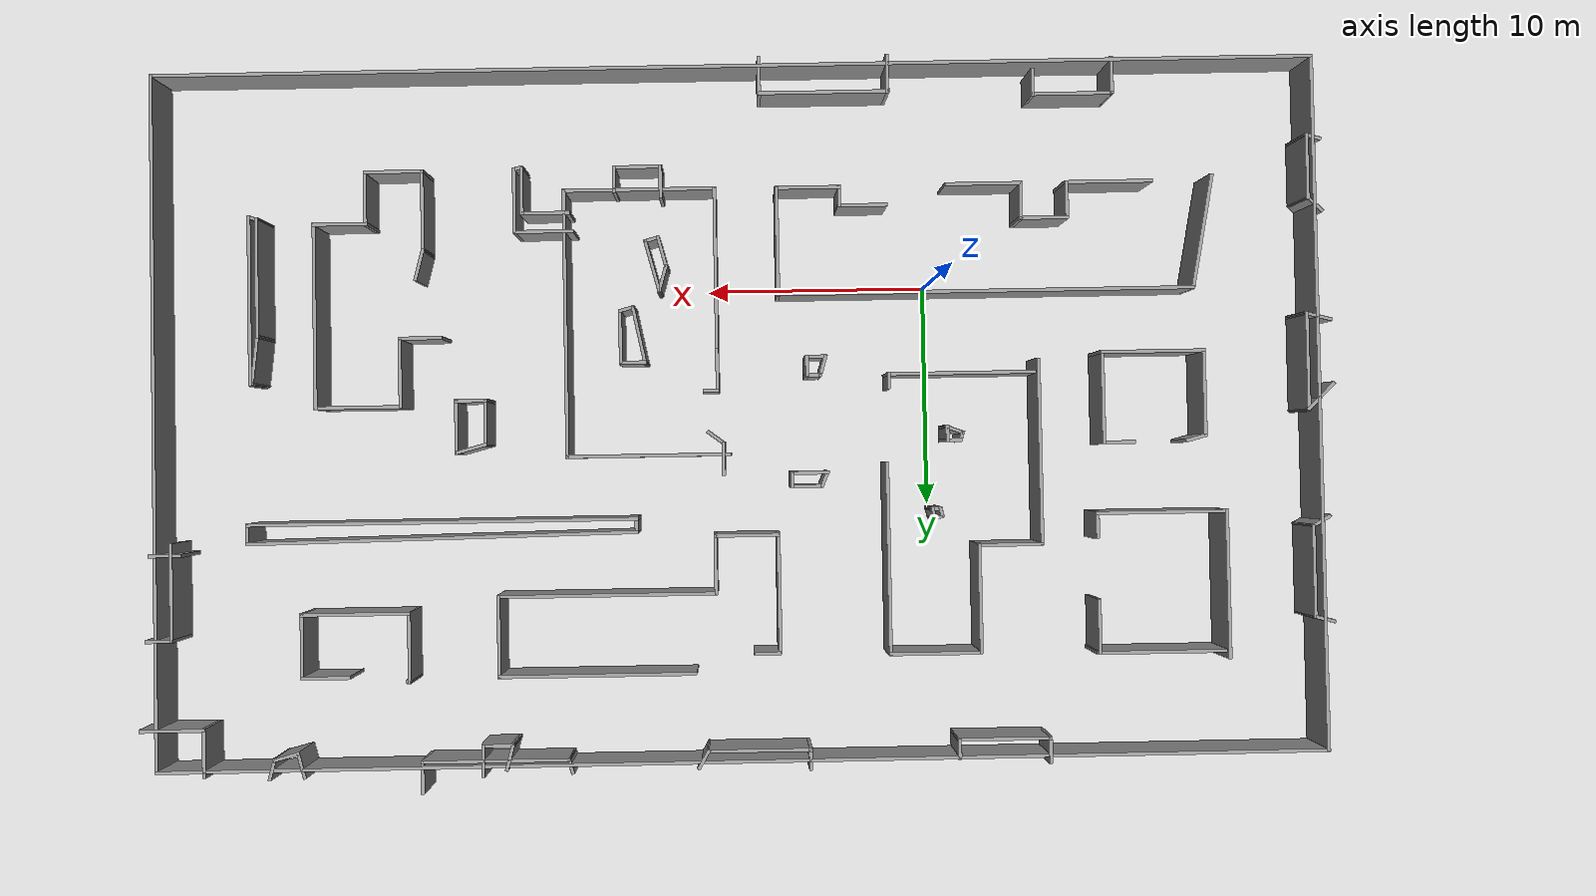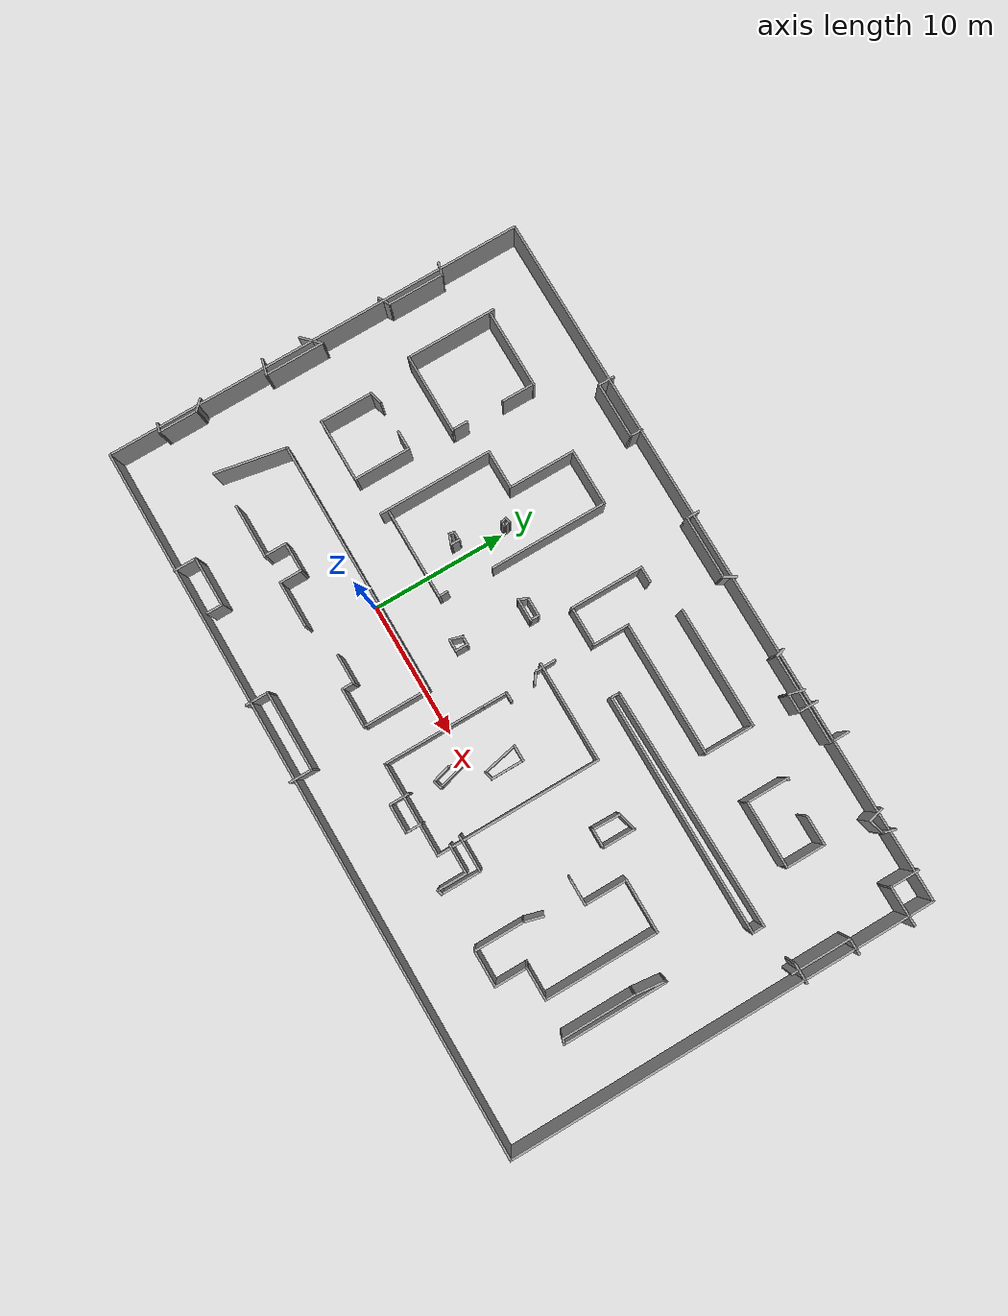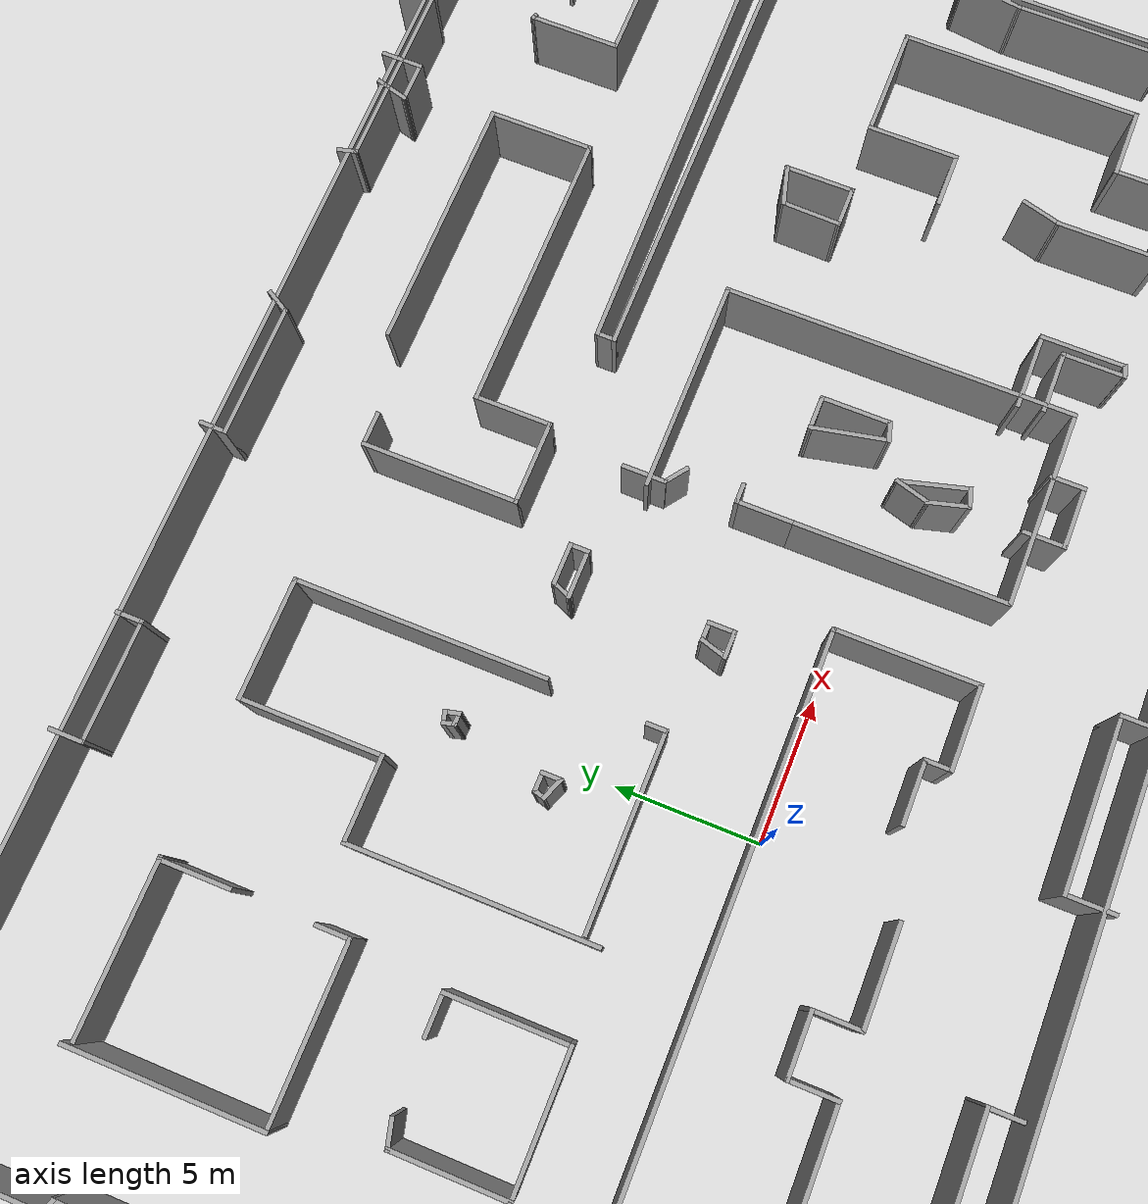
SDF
<?xml version='1.0'?>
<sdf version='1.6'>
  <model name='big_bad_building'>
    <pose frame=''>8.83669 6.06716 0 0 -0 0</pose>
    <link name='Wall_100'>
      <collision name='Wall_100_Collision'>
        <geometry>
          <box>
            <size>1.75 0.15 2.5</size>
          </box>
        </geometry>
        <pose frame=''>0 0 1.25 0 -0 0</pose>
      </collision>
      <visual name='Wall_100_Visual'>
        <pose frame=''>0 0 1.25 0 -0 0</pose>
        <geometry>
          <box>
            <size>1.75 0.15 2.5</size>
          </box>
        </geometry>
        <material>
          <script>
            <uri>file://media/materials/scripts/gazebo.material</uri>
            <name>Gazebo/Grey</name>
          </script>
          <ambient>1 1 1 1</ambient>
        </material>
        <meta>
          <layer>0</layer>
        </meta>
      </visual>
      <pose frame=''>-17.3463 -15.4498 0 0 -0 1.5708</pose>
    </link>
    <link name='Wall_101'>
      <collision name='Wall_101_Collision'>
        <geometry>
          <box>
            <size>3.75 0.15 2.5</size>
          </box>
        </geometry>
        <pose frame=''>0 0 1.25 0 -0 0</pose>
      </collision>
      <visual name='Wall_101_Visual'>
        <pose frame=''>0 0 1.25 0 -0 0</pose>
        <geometry>
          <box>
            <size>3.75 0.15 2.5</size>
          </box>
        </geometry>
        <material>
          <script>
            <uri>file://media/materials/scripts/gazebo.material</uri>
            <name>Gazebo/Grey</name>
          </script>
          <ambient>1 1 1 1</ambient>
        </material>
        <meta>
          <layer>0</layer>
        </meta>
      </visual>
      <pose frame=''>-15.5463 -14.6498 0 0 -0 0</pose>
    </link>
    <link name='Wall_102'>
      <collision name='Wall_102_Collision'>
        <geometry>
          <box>
            <size>1.25 0.15 2.5</size>
          </box>
        </geometry>
        <pose frame=''>0 0 1.25 0 -0 0</pose>
      </collision>
      <visual name='Wall_102_Visual'>
        <pose frame=''>0 0 1.25 0 -0 0</pose>
        <geometry>
          <box>
            <size>1.25 0.15 2.5</size>
          </box>
        </geometry>
        <material>
          <script>
            <uri>file://media/materials/scripts/gazebo.material</uri>
            <name>Gazebo/Grey</name>
          </script>
          <ambient>1 1 1 1</ambient>
        </material>
        <meta>
          <layer>0</layer>
        </meta>
      </visual>
      <pose frame=''>-13.7463 -15.1998 0 0 -0 -1.5708</pose>
    </link>
    <link name='Wall_104'>
      <collision name='Wall_104_Collision'>
        <geometry>
          <box>
            <size>1.75 0.15 2.5</size>
          </box>
        </geometry>
        <pose frame=''>0 0 1.25 0 -0 0</pose>
      </collision>
      <visual name='Wall_104_Visual'>
        <pose frame=''>0 0 1.25 0 -0 0</pose>
        <geometry>
          <box>
            <size>1.75 0.15 2.5</size>
          </box>
        </geometry>
        <material>
          <script>
            <uri>file://media/materials/scripts/gazebo.material</uri>
            <name>Gazebo/Grey</name>
          </script>
          <ambient>1 1 1 1</ambient>
        </material>
        <meta>
          <layer>0</layer>
        </meta>
      </visual>
      <pose frame=''>-7.13039 -15.7037 0 0 -0 1.5708</pose>
    </link>
    <link name='Wall_105'>
      <collision name='Wall_105_Collision'>
        <geometry>
          <box>
            <size>6 0.15 2.5</size>
          </box>
        </geometry>
        <pose frame=''>0 0 1.25 0 -0 0</pose>
      </collision>
      <visual name='Wall_105_Visual'>
        <pose frame=''>0 0 1.25 0 -0 0</pose>
        <geometry>
          <box>
            <size>6 0.15 2.5</size>
          </box>
        </geometry>
        <material>
          <script>
            <uri>file://media/materials/scripts/gazebo.material</uri>
            <name>Gazebo/Grey</name>
          </script>
          <ambient>1 1 1 1</ambient>
        </material>
        <meta>
          <layer>0</layer>
        </meta>
      </visual>
      <pose frame=''>-4.20539 -14.9037 0 0 -0 0</pose>
    </link>
    <link name='Wall_106'>
      <collision name='Wall_106_Collision'>
        <geometry>
          <box>
            <size>1.75 0.15 2.5</size>
          </box>
        </geometry>
        <pose frame=''>0 0 1.25 0 -0 0</pose>
      </collision>
      <visual name='Wall_106_Visual'>
        <pose frame=''>0 0 1.25 0 -0 0</pose>
        <geometry>
          <box>
            <size>1.75 0.15 2.5</size>
          </box>
        </geometry>
        <material>
          <script>
            <uri>file://media/materials/scripts/gazebo.material</uri>
            <name>Gazebo/Grey</name>
          </script>
          <ambient>1 1 1 1</ambient>
        </material>
        <meta>
          <layer>0</layer>
        </meta>
      </visual>
      <pose frame=''>-1.28039 -15.7037 0 0 -0 -1.5708</pose>
    </link>
    <link name='Wall_108'>
      <collision name='Wall_108_Collision'>
        <geometry>
          <box>
            <size>1.5 0.15 2.5</size>
          </box>
        </geometry>
        <pose frame=''>0 0 1.25 0 -0 0</pose>
      </collision>
      <visual name='Wall_108_Visual'>
        <pose frame=''>0 0 1.25 0 -0 0</pose>
        <geometry>
          <box>
            <size>1.5 0.15 2.5</size>
          </box>
        </geometry>
        <material>
          <script>
            <uri>file://media/materials/scripts/gazebo.material</uri>
            <name>Gazebo/Grey</name>
          </script>
          <ambient>1 1 1 1</ambient>
        </material>
        <meta>
          <layer>0</layer>
        </meta>
      </visual>
      <pose frame=''>3.27589 -10.9603 0 0 -0 -1.5708</pose>
    </link>
    <link name='Wall_109'>
      <collision name='Wall_109_Collision'>
        <geometry>
          <box>
            <size>2.25 0.15 2.5</size>
          </box>
        </geometry>
        <pose frame=''>0 0 1.25 0 -0 0</pose>
      </collision>
      <visual name='Wall_109_Visual'>
        <pose frame=''>0 0 1.25 0 -0 0</pose>
        <geometry>
          <box>
            <size>2.25 0.15 2.5</size>
          </box>
        </geometry>
        <material>
          <script>
            <uri>file://media/materials/scripts/gazebo.material</uri>
            <name>Gazebo/Grey</name>
          </script>
          <ambient>1 1 1 1</ambient>
        </material>
        <meta>
          <layer>0</layer>
        </meta>
      </visual>
      <pose frame=''>4.32589 -11.6353 0 0 -0 0</pose>
    </link>
    <link name='Wall_11'>
      <collision name='Wall_11_Collision'>
        <geometry>
          <box>
            <size>6.75 0.15 2.5</size>
          </box>
        </geometry>
        <pose frame=''>0 0 1.25 0 -0 0</pose>
      </collision>
      <visual name='Wall_11_Visual'>
        <pose frame=''>0 0 1.25 0 -0 0</pose>
        <geometry>
          <box>
            <size>6.75 0.15 2.5</size>
          </box>
        </geometry>
        <material>
          <script>
            <uri>file://media/materials/scripts/gazebo.material</uri>
            <name>Gazebo/Grey</name>
          </script>
          <ambient>1 1 1 1</ambient>
        </material>
        <meta>
          <layer>0</layer>
        </meta>
      </visual>
      <pose frame=''>-22.1035 7.75425 0 0 -0 -1.5708</pose>
    </link>
    <link name='Wall_110'>
      <collision name='Wall_110_Collision'>
        <geometry>
          <box>
            <size>1.25 0.15 2.5</size>
          </box>
        </geometry>
        <pose frame=''>0 0 1.25 0 -0 0</pose>
      </collision>
      <visual name='Wall_110_Visual'>
        <pose frame=''>0 0 1.25 0 -0 0</pose>
        <geometry>
          <box>
            <size>1.25 0.15 2.5</size>
          </box>
        </geometry>
        <material>
          <script>
            <uri>file://media/materials/scripts/gazebo.material</uri>
            <name>Gazebo/Grey</name>
          </script>
          <ambient>1 1 1 1</ambient>
        </material>
        <meta>
          <layer>0</layer>
        </meta>
      </visual>
      <pose frame=''>5.37589 -11.0853 0 0 -0 1.5708</pose>
    </link>
    <link name='Wall_112'>
      <collision name='Wall_112_Collision'>
        <geometry>
          <box>
            <size>2 0.15 2.5</size>
          </box>
        </geometry>
        <pose frame=''>0 0 1.25 0 -0 0</pose>
      </collision>
      <visual name='Wall_112_Visual'>
        <pose frame=''>0 0 1.25 0 -0 0</pose>
        <geometry>
          <box>
            <size>2 0.15 2.5</size>
          </box>
        </geometry>
        <material>
          <script>
            <uri>file://media/materials/scripts/gazebo.material</uri>
            <name>Gazebo/Grey</name>
          </script>
          <ambient>1 1 1 1</ambient>
        </material>
        <meta>
          <layer>0</layer>
        </meta>
      </visual>
      <pose frame=''>14.2899 -4.00343 0 0 -0 0</pose>
    </link>
    <link name='Wall_113'>
      <collision name='Wall_113_Collision'>
        <geometry>
          <box>
            <size>3.25 0.15 2.5</size>
          </box>
        </geometry>
        <pose frame=''>0 0 1.25 0 -0 0</pose>
      </collision>
      <visual name='Wall_113_Visual'>
        <pose frame=''>0 0 1.25 0 -0 0</pose>
        <geometry>
          <box>
            <size>3.25 0.15 2.5</size>
          </box>
        </geometry>
        <material>
          <script>
            <uri>file://media/materials/scripts/gazebo.material</uri>
            <name>Gazebo/Grey</name>
          </script>
          <ambient>1 1 1 1</ambient>
        </material>
        <meta>
          <layer>0</layer>
        </meta>
      </visual>
      <pose frame=''>15.2149 -2.45343 0 0 -0 1.5708</pose>
    </link>
    <link name='Wall_114'>
      <collision name='Wall_114_Collision'>
        <geometry>
          <box>
            <size>4 0.15 2.5</size>
          </box>
        </geometry>
        <pose frame=''>0 0 1.25 0 -0 0</pose>
      </collision>
      <visual name='Wall_114_Visual'>
        <pose frame=''>0 0 1.25 0 -0 0</pose>
        <geometry>
          <box>
            <size>4 0.15 2.5</size>
          </box>
        </geometry>
        <material>
          <script>
            <uri>file://media/materials/scripts/gazebo.material</uri>
            <name>Gazebo/Grey</name>
          </script>
          <ambient>1 1 1 1</ambient>
        </material>
        <meta>
          <layer>0</layer>
        </meta>
      </visual>
      <pose frame=''>17.1399 -0.903431 0 0 -0 0</pose>
    </link>
    <link name='Wall_115'>
      <collision name='Wall_115_Collision'>
        <geometry>
          <box>
            <size>8.5 0.15 2.5</size>
          </box>
        </geometry>
        <pose frame=''>0 0 1.25 0 -0 0</pose>
      </collision>
      <visual name='Wall_115_Visual'>
        <pose frame=''>0 0 1.25 0 -0 0</pose>
        <geometry>
          <box>
            <size>8.5 0.15 2.5</size>
          </box>
        </geometry>
        <material>
          <script>
            <uri>file://media/materials/scripts/gazebo.material</uri>
            <name>Gazebo/Grey</name>
          </script>
          <ambient>1 1 1 1</ambient>
        </material>
        <meta>
          <layer>0</layer>
        </meta>
      </visual>
      <pose frame=''>19.0649 -5.07843 0 0 -0 -1.5708</pose>
    </link>
    <link name='Wall_116'>
      <collision name='Wall_116_Collision'>
        <geometry>
          <box>
            <size>2.5 0.15 2.5</size>
          </box>
        </geometry>
        <pose frame=''>0 0 1.25 0 -0 0</pose>
      </collision>
      <visual name='Wall_116_Visual'>
        <pose frame=''>0 0 1.25 0 -0 0</pose>
        <geometry>
          <box>
            <size>2.5 0.15 2.5</size>
          </box>
        </geometry>
        <material>
          <script>
            <uri>file://media/materials/scripts/gazebo.material</uri>
            <name>Gazebo/Grey</name>
          </script>
          <ambient>1 1 1 1</ambient>
        </material>
        <meta>
          <layer>0</layer>
        </meta>
      </visual>
      <pose frame=''>17.8899 -9.25343 0 0 -0 3.14159</pose>
    </link>
    <link name='Wall_117'>
      <collision name='Wall_117_Collision'>
        <geometry>
          <box>
            <size>2.5 0.15 2.5</size>
          </box>
        </geometry>
        <pose frame=''>0 0 1.25 0 -0 0</pose>
      </collision>
      <visual name='Wall_117_Visual'>
        <pose frame=''>0 0 1.25 0 -0 0</pose>
        <geometry>
          <box>
            <size>2.5 0.15 2.5</size>
          </box>
        </geometry>
        <material>
          <script>
            <uri>file://media/materials/scripts/gazebo.material</uri>
            <name>Gazebo/Grey</name>
          </script>
          <ambient>1 1 1 1</ambient>
        </material>
        <meta>
          <layer>0</layer>
        </meta>
      </visual>
      <pose frame=''>16.7149 -10.4284 0 0 -0 -1.5708</pose>
    </link>
    <link name='Wall_118'>
      <collision name='Wall_118_Collision'>
        <geometry>
          <box>
            <size>2.75 0.15 2.5</size>
          </box>
        </geometry>
        <pose frame=''>0 0 1.25 0 -0 0</pose>
      </collision>
      <visual name='Wall_118_Visual'>
        <pose frame=''>0 0 1.25 0 -0 0</pose>
        <geometry>
          <box>
            <size>2.75 0.15 2.5</size>
          </box>
        </geometry>
        <material>
          <script>
            <uri>file://media/materials/scripts/gazebo.material</uri>
            <name>Gazebo/Grey</name>
          </script>
          <ambient>1 1 1 1</ambient>
        </material>
        <meta>
          <layer>0</layer>
        </meta>
      </visual>
      <pose frame=''>15.4149 -11.6034 0 0 -0 3.14159</pose>
    </link>
    <link name='Wall_119'>
      <collision name='Wall_119_Collision'>
        <geometry>
          <box>
            <size>3.75 0.15 2.5</size>
          </box>
        </geometry>
        <pose frame=''>0 0 1.25 0 -0 0</pose>
      </collision>
      <visual name='Wall_119_Visual'>
        <pose frame=''>0 0 1.25 0 -0 0</pose>
        <geometry>
          <box>
            <size>3.75 0.15 2.5</size>
          </box>
        </geometry>
        <material>
          <script>
            <uri>file://media/materials/scripts/gazebo.material</uri>
            <name>Gazebo/Grey</name>
          </script>
          <ambient>1 1 1 1</ambient>
        </material>
        <meta>
          <layer>0</layer>
        </meta>
      </visual>
      <pose frame=''>14.1149 -9.80343 0 0 -0 1.5708</pose>
    </link>
    <link name='Wall_12'>
      <collision name='Wall_12_Collision'>
        <geometry>
          <box>
            <size>6 0.15 2.5</size>
          </box>
        </geometry>
        <pose frame=''>0 0 1.25 0 -0 0</pose>
      </collision>
      <visual name='Wall_12_Visual'>
        <pose frame=''>0 0 1.25 0 -0 0</pose>
        <geometry>
          <box>
            <size>6 0.15 2.5</size>
          </box>
        </geometry>
        <material>
          <script>
            <uri>file://media/materials/scripts/gazebo.material</uri>
            <name>Gazebo/Grey</name>
          </script>
          <ambient>1 1 1 1</ambient>
        </material>
        <meta>
          <layer>0</layer>
        </meta>
      </visual>
      <pose frame=''>-19.1785 4.45425 0 0 -0 0</pose>
    </link>
    <link name='Wall_120'>
      <collision name='Wall_120_Collision'>
        <geometry>
          <box>
            <size>1.5 0.15 2.5</size>
          </box>
        </geometry>
        <pose frame=''>0 0 1.25 0 -0 0</pose>
      </collision>
      <visual name='Wall_120_Visual'>
        <pose frame=''>0 0 1.25 0 -0 0</pose>
        <geometry>
          <box>
            <size>1.5 0.15 2.5</size>
          </box>
        </geometry>
        <material>
          <script>
            <uri>file://media/materials/scripts/gazebo.material</uri>
            <name>Gazebo/Grey</name>
          </script>
          <ambient>1 1 1 1</ambient>
        </material>
        <meta>
          <layer>0</layer>
        </meta>
      </visual>
      <pose frame=''>14.2896 -7.35143 0 0 -0 1.309</pose>
    </link>
    <link name='Wall_122'>
      <collision name='Wall_122_Collision'>
        <geometry>
          <box>
            <size>1.5 0.15 2.5</size>
          </box>
        </geometry>
        <pose frame=''>0 0 1.25 0 -0 0</pose>
      </collision>
      <visual name='Wall_122_Visual'>
        <pose frame=''>0 0 1.25 0 -0 0</pose>
        <geometry>
          <box>
            <size>1.5 0.15 2.5</size>
          </box>
        </geometry>
        <material>
          <script>
            <uri>file://media/materials/scripts/gazebo.material</uri>
            <name>Gazebo/Grey</name>
          </script>
          <ambient>1 1 1 1</ambient>
        </material>
        <meta>
          <layer>0</layer>
        </meta>
      </visual>
      <pose frame=''>12.0499 1.05715 0 0 -0 0.261799</pose>
    </link>
    <link name='Wall_123'>
      <collision name='Wall_123_Collision'>
        <geometry>
          <box>
            <size>2.5 0.15 2.5</size>
          </box>
        </geometry>
        <pose frame=''>0 0 1.25 0 -0 0</pose>
      </collision>
      <visual name='Wall_123_Visual'>
        <pose frame=''>0 0 1.25 0 -0 0</pose>
        <geometry>
          <box>
            <size>2.5 0.15 2.5</size>
          </box>
        </geometry>
        <material>
          <script>
            <uri>file://media/materials/scripts/gazebo.material</uri>
            <name>Gazebo/Grey</name>
          </script>
          <ambient>1 1 1 1</ambient>
        </material>
        <meta>
          <layer>0</layer>
        </meta>
      </visual>
      <pose frame=''>12.7019 0.056852 0 0 -0 -1.5708</pose>
    </link>
    <link name='Wall_124'>
      <collision name='Wall_124_Collision'>
        <geometry>
          <box>
            <size>1.5 0.15 2.5</size>
          </box>
        </geometry>
        <pose frame=''>0 0 1.25 0 -0 0</pose>
      </collision>
      <visual name='Wall_124_Visual'>
        <pose frame=''>0 0 1.25 0 -0 0</pose>
        <geometry>
          <box>
            <size>1.5 0.15 2.5</size>
          </box>
        </geometry>
        <material>
          <script>
            <uri>file://media/materials/scripts/gazebo.material</uri>
            <name>Gazebo/Grey</name>
          </script>
          <ambient>1 1 1 1</ambient>
        </material>
        <meta>
          <layer>0</layer>
        </meta>
      </visual>
      <pose frame=''>12.0269 -1.11815 0 0 -0 3.14159</pose>
    </link>
    <link name='Wall_125'>
      <collision name='Wall_125_Collision'>
        <geometry>
          <box>
            <size>2.15112 0.15 2.5</size>
          </box>
        </geometry>
        <pose frame=''>0 0 1.25 0 -0 0</pose>
      </collision>
      <visual name='Wall_125_Visual'>
        <pose frame=''>0 0 1.25 0 -0 0</pose>
        <geometry>
          <box>
            <size>2.15112 0.15 2.5</size>
          </box>
        </geometry>
        <material>
          <script>
            <uri>file://media/materials/scripts/gazebo.material</uri>
            <name>Gazebo/Grey</name>
          </script>
          <ambient>1 1 1 1</ambient>
        </material>
        <meta>
          <layer>0</layer>
        </meta>
      </visual>
      <pose frame=''>11.3749 -0.117851 0 0 -0 1.54781</pose>
    </link>
    <link name='Wall_127'>
      <collision name='Wall_127_Collision'>
        <geometry>
          <box>
            <size>5.5 0.15 2.5</size>
          </box>
        </geometry>
        <pose frame=''>0 0 1.25 0 -0 0</pose>
      </collision>
      <visual name='Wall_127_Visual'>
        <pose frame=''>0 0 1.25 0 -0 0</pose>
        <geometry>
          <box>
            <size>5.5 0.15 2.5</size>
          </box>
        </geometry>
        <material>
          <script>
            <uri>file://media/materials/scripts/gazebo.material</uri>
            <name>Gazebo/Grey</name>
          </script>
          <ambient>1 1 1 1</ambient>
        </material>
        <meta>
          <layer>0</layer>
        </meta>
      </visual>
      <pose frame=''>21.6773 -6.86879 0 0 -0 -1.5708</pose>
    </link>
    <link name='Wall_128'>
      <collision name='Wall_128_Collision'>
        <geometry>
          <box>
            <size>0.5 0.15 2.5</size>
          </box>
        </geometry>
        <pose frame=''>0 0 1.25 0 -0 0</pose>
      </collision>
      <visual name='Wall_128_Visual'>
        <pose frame=''>0 0 1.25 0 -0 0</pose>
        <geometry>
          <box>
            <size>0.5 0.15 2.5</size>
          </box>
        </geometry>
        <material>
          <script>
            <uri>file://media/materials/scripts/gazebo.material</uri>
            <name>Gazebo/Grey</name>
          </script>
          <ambient>1 1 1 1</ambient>
        </material>
        <meta>
          <layer>0</layer>
        </meta>
      </visual>
      <pose frame=''>21.8463 -9.58908 0 0 -0 -0.261799</pose>
    </link>
    <link name='Wall_129'>
      <collision name='Wall_129_Collision'>
        <geometry>
          <box>
            <size>7.75 0.15 2.5</size>
          </box>
        </geometry>
        <pose frame=''>0 0 1.25 0 -0 0</pose>
      </collision>
      <visual name='Wall_129_Visual'>
        <pose frame=''>0 0 1.25 0 -0 0</pose>
        <geometry>
          <box>
            <size>7.75 0.15 2.5</size>
          </box>
        </geometry>
        <material>
          <script>
            <uri>file://media/materials/scripts/gazebo.material</uri>
            <name>Gazebo/Grey</name>
          </script>
          <ambient>1 1 1 1</ambient>
        </material>
        <meta>
          <layer>0</layer>
        </meta>
      </visual>
      <pose frame=''>22.0153 -5.83438 0 0 -0 1.5708</pose>
    </link>
    <link name='Wall_13'>
      <collision name='Wall_13_Collision'>
        <geometry>
          <box>
            <size>1.25 0.15 2.5</size>
          </box>
        </geometry>
        <pose frame=''>0 0 1.25 0 -0 0</pose>
      </collision>
      <visual name='Wall_13_Visual'>
        <pose frame=''>0 0 1.25 0 -0 0</pose>
        <geometry>
          <box>
            <size>1.25 0.15 2.5</size>
          </box>
        </geometry>
        <material>
          <script>
            <uri>file://media/materials/scripts/gazebo.material</uri>
            <name>Gazebo/Grey</name>
          </script>
          <ambient>1 1 1 1</ambient>
        </material>
        <meta>
          <layer>0</layer>
        </meta>
      </visual>
      <pose frame=''>-16.2535 5.00425 0 0 -0 1.5708</pose>
    </link>
    <link name='Wall_130'>
      <collision name='Wall_130_Collision'>
        <geometry>
          <box>
            <size>0.25 0.15 2.5</size>
          </box>
        </geometry>
        <pose frame=''>0 0 1.25 0 -0 0</pose>
      </collision>
      <visual name='Wall_130_Visual'>
        <pose frame=''>0 0 1.25 0 -0 0</pose>
        <geometry>
          <box>
            <size>0.25 0.15 2.5</size>
          </box>
        </geometry>
        <material>
          <script>
            <uri>file://media/materials/scripts/gazebo.material</uri>
            <name>Gazebo/Grey</name>
          </script>
          <ambient>1 1 1 1</ambient>
        </material>
        <meta>
          <layer>0</layer>
        </meta>
      </visual>
      <pose frame=''>21.972 -2.05938 0 0 -0 -2.61799</pose>
    </link>
    <link name='Wall_131'>
      <collision name='Wall_131_Collision'>
        <geometry>
          <box>
            <size>2.27435 0.15 2.5</size>
          </box>
        </geometry>
        <pose frame=''>0 0 1.25 0 -0 0</pose>
      </collision>
      <visual name='Wall_131_Visual'>
        <pose frame=''>0 0 1.25 0 -0 0</pose>
        <geometry>
          <box>
            <size>2.27435 0.15 2.5</size>
          </box>
        </geometry>
        <material>
          <script>
            <uri>file://media/materials/scripts/gazebo.material</uri>
            <name>Gazebo/Grey</name>
          </script>
          <ambient>1 1 1 1</ambient>
        </material>
        <meta>
          <layer>0</layer>
        </meta>
      </visual>
      <pose frame=''>21.803 -3.13908 0 0 -0 -1.68945</pose>
    </link>
    <link name='Wall_133'>
      <collision name='Wall_133_Collision'>
        <geometry>
          <box>
            <size>2.75 0.15 2.5</size>
          </box>
        </geometry>
        <pose frame=''>0 0 1.25 0 -0 0</pose>
      </collision>
      <visual name='Wall_133_Visual'>
        <pose frame=''>0 0 1.25 0 -0 0</pose>
        <geometry>
          <box>
            <size>2.75 0.15 2.5</size>
          </box>
        </geometry>
        <material>
          <script>
            <uri>file://media/materials/scripts/gazebo.material</uri>
            <name>Gazebo/Grey</name>
          </script>
          <ambient>1 1 1 1</ambient>
        </material>
        <meta>
          <layer>0</layer>
        </meta>
      </visual>
      <pose frame=''>8.63688 -8.7624 0 0 -0 0</pose>
    </link>
    <link name='Wall_134'>
      <collision name='Wall_134_Collision'>
        <geometry>
          <box>
            <size>3 0.15 2.5</size>
          </box>
        </geometry>
        <pose frame=''>0 0 1.25 0 -0 0</pose>
      </collision>
      <visual name='Wall_134_Visual'>
        <pose frame=''>0 0 1.25 0 -0 0</pose>
        <geometry>
          <box>
            <size>3 0.15 2.5</size>
          </box>
        </geometry>
        <material>
          <script>
            <uri>file://media/materials/scripts/gazebo.material</uri>
            <name>Gazebo/Grey</name>
          </script>
          <ambient>1 1 1 1</ambient>
        </material>
        <meta>
          <layer>0</layer>
        </meta>
      </visual>
      <pose frame=''>9.93688 -10.1874 0 0 -0 -1.5708</pose>
    </link>
    <link name='Wall_135'>
      <collision name='Wall_135_Collision'>
        <geometry>
          <box>
            <size>0.5 0.15 2.5</size>
          </box>
        </geometry>
        <pose frame=''>0 0 1.25 0 -0 0</pose>
      </collision>
      <visual name='Wall_135_Visual'>
        <pose frame=''>0 0 1.25 0 -0 0</pose>
        <geometry>
          <box>
            <size>0.5 0.15 2.5</size>
          </box>
        </geometry>
        <material>
          <script>
            <uri>file://media/materials/scripts/gazebo.material</uri>
            <name>Gazebo/Grey</name>
          </script>
          <ambient>1 1 1 1</ambient>
        </material>
        <meta>
          <layer>0</layer>
        </meta>
      </visual>
      <pose frame=''>9.76784 -11.6577 0 0 -0 -2.87979</pose>
    </link>
    <link name='Wall_136'>
      <collision name='Wall_136_Collision'>
        <geometry>
          <box>
            <size>2.25 0.15 2.5</size>
          </box>
        </geometry>
        <pose frame=''>0 0 1.25 0 -0 0</pose>
      </collision>
      <visual name='Wall_136_Visual'>
        <pose frame=''>0 0 1.25 0 -0 0</pose>
        <geometry>
          <box>
            <size>2.25 0.15 2.5</size>
          </box>
        </geometry>
        <material>
          <script>
            <uri>file://media/materials/scripts/gazebo.material</uri>
            <name>Gazebo/Grey</name>
          </script>
          <ambient>1 1 1 1</ambient>
        </material>
        <meta>
          <layer>0</layer>
        </meta>
      </visual>
      <pose frame=''>9.59881 -10.653 0 0 -0 1.5708</pose>
    </link>
    <link name='Wall_137'>
      <collision name='Wall_137_Collision'>
        <geometry>
          <box>
            <size>2.25 0.15 2.5</size>
          </box>
        </geometry>
        <pose frame=''>0 0 1.25 0 -0 0</pose>
      </collision>
      <visual name='Wall_137_Visual'>
        <pose frame=''>0 0 1.25 0 -0 0</pose>
        <geometry>
          <box>
            <size>2.25 0.15 2.5</size>
          </box>
        </geometry>
        <material>
          <script>
            <uri>file://media/materials/scripts/gazebo.material</uri>
            <name>Gazebo/Grey</name>
          </script>
          <ambient>1 1 1 1</ambient>
        </material>
        <meta>
          <layer>0</layer>
        </meta>
      </visual>
      <pose frame=''>8.54881 -9.60299 0 0 -0 3.14159</pose>
    </link>
    <link name='Wall_139'>
      <collision name='Wall_139_Collision'>
        <geometry>
          <box>
            <size>1.75 0.15 2.5</size>
          </box>
        </geometry>
        <pose frame=''>0 0 1.25 0 -0 0</pose>
      </collision>
      <visual name='Wall_139_Visual'>
        <pose frame=''>0 0 1.25 0 -0 0</pose>
        <geometry>
          <box>
            <size>1.75 0.15 2.5</size>
          </box>
        </geometry>
        <material>
          <script>
            <uri>file://media/materials/scripts/gazebo.material</uri>
            <name>Gazebo/Grey</name>
          </script>
          <ambient>1 1 1 1</ambient>
        </material>
        <meta>
          <layer>0</layer>
        </meta>
      </visual>
      <pose frame=''>-3.28465 2.40532 0 0 -0 0</pose>
    </link>
    <link name='Wall_140'>
      <collision name='Wall_140_Collision'>
        <geometry>
          <box>
            <size>0.75 0.15 2.5</size>
          </box>
        </geometry>
        <pose frame=''>0 0 1.25 0 -0 0</pose>
      </collision>
      <visual name='Wall_140_Visual'>
        <pose frame=''>0 0 1.25 0 -0 0</pose>
        <geometry>
          <box>
            <size>0.75 0.15 2.5</size>
          </box>
        </geometry>
        <material>
          <script>
            <uri>file://media/materials/scripts/gazebo.material</uri>
            <name>Gazebo/Grey</name>
          </script>
          <ambient>1 1 1 1</ambient>
        </material>
        <meta>
          <layer>0</layer>
        </meta>
      </visual>
      <pose frame=''>-2.48465 2.70532 0 0 -0 1.5708</pose>
    </link>
    <link name='Wall_141'>
      <collision name='Wall_141_Collision'>
        <geometry>
          <box>
            <size>1.5 0.15 2.5</size>
          </box>
        </geometry>
        <pose frame=''>0 0 1.25 0 -0 0</pose>
      </collision>
      <visual name='Wall_141_Visual'>
        <pose frame=''>0 0 1.25 0 -0 0</pose>
        <geometry>
          <box>
            <size>1.5 0.15 2.5</size>
          </box>
        </geometry>
        <material>
          <script>
            <uri>file://media/materials/scripts/gazebo.material</uri>
            <name>Gazebo/Grey</name>
          </script>
          <ambient>1 1 1 1</ambient>
        </material>
        <meta>
          <layer>0</layer>
        </meta>
      </visual>
      <pose frame=''>-3.15965 3.00532 0 0 -0 3.14159</pose>
    </link>
    <link name='Wall_142'>
      <collision name='Wall_142_Collision'>
        <geometry>
          <box>
            <size>0.8 0.15 2.5</size>
          </box>
        </geometry>
        <pose frame=''>0 0 1.25 0 -0 0</pose>
      </collision>
      <visual name='Wall_142_Visual'>
        <pose frame=''>0 0 1.25 0 -0 0</pose>
        <geometry>
          <box>
            <size>0.8 0.15 2.5</size>
          </box>
        </geometry>
        <material>
          <script>
            <uri>file://media/materials/scripts/gazebo.material</uri>
            <name>Gazebo/Grey</name>
          </script>
          <ambient>1 1 1 1</ambient>
        </material>
        <meta>
          <layer>0</layer>
        </meta>
      </visual>
      <pose frame=''>-3.95965 2.70532 0 0 -0 -1.96559</pose>
    </link>
    <link name='Wall_144'>
      <collision name='Wall_144_Collision'>
        <geometry>
          <box>
            <size>1.25 0.15 2.5</size>
          </box>
        </geometry>
        <pose frame=''>0 0 1.25 0 -0 0</pose>
      </collision>
      <visual name='Wall_144_Visual'>
        <pose frame=''>0 0 1.25 0 -0 0</pose>
        <geometry>
          <box>
            <size>1.25 0.15 2.5</size>
          </box>
        </geometry>
        <material>
          <script>
            <uri>file://media/materials/scripts/gazebo.material</uri>
            <name>Gazebo/Grey</name>
          </script>
          <ambient>1 1 1 1</ambient>
        </material>
        <meta>
          <layer>0</layer>
        </meta>
      </visual>
      <pose frame=''>-13.913 15.0993 0 0 -0 -1.5708</pose>
    </link>
    <link name='Wall_145'>
      <collision name='Wall_145_Collision'>
        <geometry>
          <box>
            <size>4.25 0.15 2.5</size>
          </box>
        </geometry>
        <pose frame=''>0 0 1.25 0 -0 0</pose>
      </collision>
      <visual name='Wall_145_Visual'>
        <pose frame=''>0 0 1.25 0 -0 0</pose>
        <geometry>
          <box>
            <size>4.25 0.15 2.5</size>
          </box>
        </geometry>
        <material>
          <script>
            <uri>file://media/materials/scripts/gazebo.material</uri>
            <name>Gazebo/Grey</name>
          </script>
          <ambient>1 1 1 1</ambient>
        </material>
        <meta>
          <layer>0</layer>
        </meta>
      </visual>
      <pose frame=''>-11.863 14.5493 0 0 -0 0</pose>
    </link>
    <link name='Wall_146'>
      <collision name='Wall_146_Collision'>
        <geometry>
          <box>
            <size>1 0.15 2.5</size>
          </box>
        </geometry>
        <pose frame=''>0 0 1.25 0 -0 0</pose>
      </collision>
      <visual name='Wall_146_Visual'>
        <pose frame=''>0 0 1.25 0 -0 0</pose>
        <geometry>
          <box>
            <size>1 0.15 2.5</size>
          </box>
        </geometry>
        <material>
          <script>
            <uri>file://media/materials/scripts/gazebo.material</uri>
            <name>Gazebo/Grey</name>
          </script>
          <ambient>1 1 1 1</ambient>
        </material>
        <meta>
          <layer>0</layer>
        </meta>
      </visual>
      <pose frame=''>-9.81303 14.9743 0 0 -0 1.5708</pose>
    </link>
    <link name='Wall_148'>
      <collision name='Wall_148_Collision'>
        <geometry>
          <box>
            <size>1 0.15 2.5</size>
          </box>
        </geometry>
        <pose frame=''>0 0 1.25 0 -0 0</pose>
      </collision>
      <visual name='Wall_148_Visual'>
        <pose frame=''>0 0 1.25 0 -0 0</pose>
        <geometry>
          <box>
            <size>1 0.15 2.5</size>
          </box>
        </geometry>
        <material>
          <script>
            <uri>file://media/materials/scripts/gazebo.material</uri>
            <name>Gazebo/Grey</name>
          </script>
          <ambient>1 1 1 1</ambient>
        </material>
        <meta>
          <layer>0</layer>
        </meta>
      </visual>
      <pose frame=''>-3.0878 15.3082 0 0 -0 -1.5708</pose>
    </link>
    <link name='Wall_149'>
      <collision name='Wall_149_Collision'>
        <geometry>
          <box>
            <size>4.75 0.15 2.5</size>
          </box>
        </geometry>
        <pose frame=''>0 0 1.25 0 -0 0</pose>
      </collision>
      <visual name='Wall_149_Visual'>
        <pose frame=''>0 0 1.25 0 -0 0</pose>
        <geometry>
          <box>
            <size>4.75 0.15 2.5</size>
          </box>
        </geometry>
        <material>
          <script>
            <uri>file://media/materials/scripts/gazebo.material</uri>
            <name>Gazebo/Grey</name>
          </script>
          <ambient>1 1 1 1</ambient>
        </material>
        <meta>
          <layer>0</layer>
        </meta>
      </visual>
      <pose frame=''>-0.787797 14.8832 0 0 -0 0</pose>
    </link>
    <link name='Wall_15'>
      <collision name='Wall_15_Collision'>
        <geometry>
          <box>
            <size>1.5 0.15 2.5</size>
          </box>
        </geometry>
        <pose frame=''>0 0 1.25 0 -0 0</pose>
      </collision>
      <visual name='Wall_15_Visual'>
        <pose frame=''>0 0 1.25 0 -0 0</pose>
        <geometry>
          <box>
            <size>1.5 0.15 2.5</size>
          </box>
        </geometry>
        <material>
          <script>
            <uri>file://media/materials/scripts/gazebo.material</uri>
            <name>Gazebo/Grey</name>
          </script>
          <ambient>1 1 1 1</ambient>
        </material>
        <meta>
          <layer>0</layer>
        </meta>
      </visual>
      <pose frame=''>-17.3058 1.26316 0 0 -0 0</pose>
    </link>
    <link name='Wall_150'>
      <collision name='Wall_150_Collision'>
        <geometry>
          <box>
            <size>1 0.15 2.5</size>
          </box>
        </geometry>
        <pose frame=''>0 0 1.25 0 -0 0</pose>
      </collision>
      <visual name='Wall_150_Visual'>
        <pose frame=''>0 0 1.25 0 -0 0</pose>
        <geometry>
          <box>
            <size>1 0.15 2.5</size>
          </box>
        </geometry>
        <material>
          <script>
            <uri>file://media/materials/scripts/gazebo.material</uri>
            <name>Gazebo/Grey</name>
          </script>
          <ambient>1 1 1 1</ambient>
        </material>
        <meta>
          <layer>0</layer>
        </meta>
      </visual>
      <pose frame=''>1.7247 15.2513 0 0 -0 1.0472</pose>
    </link>
    <link name='Wall_152'>
      <collision name='Wall_152_Collision'>
        <geometry>
          <box>
            <size>0.75 0.15 2.5</size>
          </box>
        </geometry>
        <pose frame=''>0 0 1.25 0 -0 0</pose>
      </collision>
      <visual name='Wall_152_Visual'>
        <pose frame=''>0 0 1.25 0 -0 0</pose>
        <geometry>
          <box>
            <size>0.75 0.15 2.5</size>
          </box>
        </geometry>
        <material>
          <script>
            <uri>file://media/materials/scripts/gazebo.material</uri>
            <name>Gazebo/Grey</name>
          </script>
          <ambient>1 1 1 1</ambient>
        </material>
        <meta>
          <layer>0</layer>
        </meta>
      </visual>
      <pose frame=''>7.73116 15.4434 0 0 -0 -1.309</pose>
    </link>
    <link name='Wall_153'>
      <collision name='Wall_153_Collision'>
        <geometry>
          <box>
            <size>6.75 0.15 2.5</size>
          </box>
        </geometry>
        <pose frame=''>0 0 1.25 0 -0 0</pose>
      </collision>
      <visual name='Wall_153_Visual'>
        <pose frame=''>0 0 1.25 0 -0 0</pose>
        <geometry>
          <box>
            <size>6.75 0.15 2.5</size>
          </box>
        </geometry>
        <material>
          <script>
            <uri>file://media/materials/scripts/gazebo.material</uri>
            <name>Gazebo/Grey</name>
          </script>
          <ambient>1 1 1 1</ambient>
        </material>
        <meta>
          <layer>0</layer>
        </meta>
      </visual>
      <pose frame=''>11.1088 15.1537 0 0 -0 0</pose>
    </link>
    <link name='Wall_154'>
      <collision name='Wall_154_Collision'>
        <geometry>
          <box>
            <size>1.5 0.15 2.5</size>
          </box>
        </geometry>
        <pose frame=''>0 0 1.25 0 -0 0</pose>
      </collision>
      <visual name='Wall_154_Visual'>
        <pose frame=''>0 0 1.25 0 -0 0</pose>
        <geometry>
          <box>
            <size>1.5 0.15 2.5</size>
          </box>
        </geometry>
        <material>
          <script>
            <uri>file://media/materials/scripts/gazebo.material</uri>
            <name>Gazebo/Grey</name>
          </script>
          <ambient>1 1 1 1</ambient>
        </material>
        <meta>
          <layer>0</layer>
        </meta>
      </visual>
      <pose frame=''>14.4088 15.8287 0 0 -0 1.5708</pose>
    </link>
    <link name='Wall_156'>
      <collision name='Wall_156_Collision'>
        <geometry>
          <box>
            <size>1.5 0.15 2.5</size>
          </box>
        </geometry>
        <pose frame=''>0 0 1.25 0 -0 0</pose>
      </collision>
      <visual name='Wall_156_Visual'>
        <pose frame=''>0 0 1.25 0 -0 0</pose>
        <geometry>
          <box>
            <size>1.5 0.15 2.5</size>
          </box>
        </geometry>
        <material>
          <script>
            <uri>file://media/materials/scripts/gazebo.material</uri>
            <name>Gazebo/Grey</name>
          </script>
          <ambient>1 1 1 1</ambient>
        </material>
        <meta>
          <layer>0</layer>
        </meta>
      </visual>
      <pose frame=''>11.6815 15.1421 0 0 -0 -1.5708</pose>
    </link>
    <link name='Wall_157'>
      <collision name='Wall_157_Collision'>
        <geometry>
          <box>
            <size>1.5 0.15 2.5</size>
          </box>
        </geometry>
        <pose frame=''>0 0 1.25 0 -0 0</pose>
      </collision>
      <visual name='Wall_157_Visual'>
        <pose frame=''>0 0 1.25 0 -0 0</pose>
        <geometry>
          <box>
            <size>1.5 0.15 2.5</size>
          </box>
        </geometry>
        <material>
          <script>
            <uri>file://media/materials/scripts/gazebo.material</uri>
            <name>Gazebo/Grey</name>
          </script>
          <ambient>1 1 1 1</ambient>
        </material>
        <meta>
          <layer>0</layer>
        </meta>
      </visual>
      <pose frame=''>11.0065 14.4671 0 0 -0 3.14159</pose>
    </link>
    <link name='Wall_158'>
      <collision name='Wall_158_Collision'>
        <geometry>
          <box>
            <size>1.25 0.15 2.5</size>
          </box>
        </geometry>
        <pose frame=''>0 0 1.25 0 -0 0</pose>
      </collision>
      <visual name='Wall_158_Visual'>
        <pose frame=''>0 0 1.25 0 -0 0</pose>
        <geometry>
          <box>
            <size>1.25 0.15 2.5</size>
          </box>
        </geometry>
        <material>
          <script>
            <uri>file://media/materials/scripts/gazebo.material</uri>
            <name>Gazebo/Grey</name>
          </script>
          <ambient>1 1 1 1</ambient>
        </material>
        <meta>
          <layer>0</layer>
        </meta>
      </visual>
      <pose frame=''>10.4739 14.9984 0 0 -0 1.309</pose>
    </link>
    <link name='Wall_16'>
      <collision name='Wall_16_Collision'>
        <geometry>
          <box>
            <size>4.25 0.15 2.5</size>
          </box>
        </geometry>
        <pose frame=''>0 0 1.25 0 -0 0</pose>
      </collision>
      <visual name='Wall_16_Visual'>
        <pose frame=''>0 0 1.25 0 -0 0</pose>
        <geometry>
          <box>
            <size>4.25 0.15 2.5</size>
          </box>
        </geometry>
        <material>
          <script>
            <uri>file://media/materials/scripts/gazebo.material</uri>
            <name>Gazebo/Grey</name>
          </script>
          <ambient>1 1 1 1</ambient>
        </material>
        <meta>
          <layer>0</layer>
        </meta>
      </visual>
      <pose frame=''>-16.6308 -0.786836 0 0 -0 -1.5708</pose>
    </link>
    <link name='Wall_160'>
      <collision name='Wall_160_Collision'>
        <geometry>
          <box>
            <size>2.25 0.15 2.5</size>
          </box>
        </geometry>
        <pose frame=''>0 0 1.25 0 -0 0</pose>
      </collision>
      <visual name='Wall_160_Visual'>
        <pose frame=''>0 0 1.25 0 -0 0</pose>
        <geometry>
          <box>
            <size>2.25 0.15 2.5</size>
          </box>
        </geometry>
        <material>
          <script>
            <uri>file://media/materials/scripts/gazebo.material</uri>
            <name>Gazebo/Grey</name>
          </script>
          <ambient>1 1 1 1</ambient>
        </material>
        <meta>
          <layer>0</layer>
        </meta>
      </visual>
      <pose frame=''>24.269 14.5993 0 0 -0 -1.5708</pose>
    </link>
    <link name='Wall_161'>
      <collision name='Wall_161_Collision'>
        <geometry>
          <box>
            <size>3 0.15 2.5</size>
          </box>
        </geometry>
        <pose frame=''>0 0 1.25 0 -0 0</pose>
      </collision>
      <visual name='Wall_161_Visual'>
        <pose frame=''>0 0 1.25 0 -0 0</pose>
        <geometry>
          <box>
            <size>3 0.15 2.5</size>
          </box>
        </geometry>
        <material>
          <script>
            <uri>file://media/materials/scripts/gazebo.material</uri>
            <name>Gazebo/Grey</name>
          </script>
          <ambient>1 1 1 1</ambient>
        </material>
        <meta>
          <layer>0</layer>
        </meta>
      </visual>
      <pose frame=''>25.694 13.5493 0 0 -0 0</pose>
    </link>
    <link name='Wall_163'>
      <collision name='Wall_163_Collision'>
        <geometry>
          <box>
            <size>1.25 0.15 2.5</size>
          </box>
        </geometry>
        <pose frame=''>0 0 1.25 0 -0 0</pose>
      </collision>
      <visual name='Wall_163_Visual'>
        <pose frame=''>0 0 1.25 0 -0 0</pose>
        <geometry>
          <box>
            <size>1.25 0.15 2.5</size>
          </box>
        </geometry>
        <material>
          <script>
            <uri>file://media/materials/scripts/gazebo.material</uri>
            <name>Gazebo/Grey</name>
          </script>
          <ambient>1 1 1 1</ambient>
        </material>
        <meta>
          <layer>0</layer>
        </meta>
      </visual>
      <pose frame=''>19.8798 15.202 0 0 -0 -1.309</pose>
    </link>
    <link name='Wall_164'>
      <collision name='Wall_164_Collision'>
        <geometry>
          <box>
            <size>1.25 0.15 2.5</size>
          </box>
        </geometry>
        <pose frame=''>0 0 1.25 0 -0 0</pose>
      </collision>
      <visual name='Wall_164_Visual'>
        <pose frame=''>0 0 1.25 0 -0 0</pose>
        <geometry>
          <box>
            <size>1.25 0.15 2.5</size>
          </box>
        </geometry>
        <material>
          <script>
            <uri>file://media/materials/scripts/gazebo.material</uri>
            <name>Gazebo/Grey</name>
          </script>
          <ambient>1 1 1 1</ambient>
        </material>
        <meta>
          <layer>0</layer>
        </meta>
      </visual>
      <pose frame=''>20.5535 14.813 0 0 -0 0.261799</pose>
    </link>
    <link name='Wall_165'>
      <collision name='Wall_165_Collision'>
        <geometry>
          <box>
            <size>1 0.15 2.5</size>
          </box>
        </geometry>
        <pose frame=''>0 0 1.25 0 -0 0</pose>
      </collision>
      <visual name='Wall_165_Visual'>
        <pose frame=''>0 0 1.25 0 -0 0</pose>
        <geometry>
          <box>
            <size>1 0.15 2.5</size>
          </box>
        </geometry>
        <material>
          <script>
            <uri>file://media/materials/scripts/gazebo.material</uri>
            <name>Gazebo/Grey</name>
          </script>
          <ambient>1 1 1 1</ambient>
        </material>
        <meta>
          <layer>0</layer>
        </meta>
      </visual>
      <pose frame=''>21.1947 15.3659 0 0 -0 1.309</pose>
    </link>
    <link name='Wall_167'>
      <collision name='Wall_167_Collision'>
        <geometry>
          <box>
            <size>1.25 0.15 2.5</size>
          </box>
        </geometry>
        <pose frame=''>0 0 1.25 0 -0 0</pose>
      </collision>
      <visual name='Wall_167_Visual'>
        <pose frame=''>0 0 1.25 0 -0 0</pose>
        <geometry>
          <box>
            <size>1.25 0.15 2.5</size>
          </box>
        </geometry>
        <material>
          <script>
            <uri>file://media/materials/scripts/gazebo.material</uri>
            <name>Gazebo/Grey</name>
          </script>
          <ambient>1 1 1 1</ambient>
        </material>
        <meta>
          <layer>0</layer>
        </meta>
      </visual>
      <pose frame=''>26.2365 9.52339 0 0 -0 3.14159</pose>
    </link>
    <link name='Wall_168'>
      <collision name='Wall_168_Collision'>
        <geometry>
          <box>
            <size>4.5 0.15 2.5</size>
          </box>
        </geometry>
        <pose frame=''>0 0 1.25 0 -0 0</pose>
      </collision>
      <visual name='Wall_168_Visual'>
        <pose frame=''>0 0 1.25 0 -0 0</pose>
        <geometry>
          <box>
            <size>4.5 0.15 2.5</size>
          </box>
        </geometry>
        <material>
          <script>
            <uri>file://media/materials/scripts/gazebo.material</uri>
            <name>Gazebo/Grey</name>
          </script>
          <ambient>1 1 1 1</ambient>
        </material>
        <meta>
          <layer>0</layer>
        </meta>
      </visual>
      <pose frame=''>25.6865 7.34839 0 0 -0 -1.5708</pose>
    </link>
    <link name='Wall_17'>
      <collision name='Wall_17_Collision'>
        <geometry>
          <box>
            <size>4.75 0.15 2.5</size>
          </box>
        </geometry>
        <pose frame=''>0 0 1.25 0 -0 0</pose>
      </collision>
      <visual name='Wall_17_Visual'>
        <pose frame=''>0 0 1.25 0 -0 0</pose>
        <geometry>
          <box>
            <size>4.75 0.15 2.5</size>
          </box>
        </geometry>
        <material>
          <script>
            <uri>file://media/materials/scripts/gazebo.material</uri>
            <name>Gazebo/Grey</name>
          </script>
          <ambient>1 1 1 1</ambient>
        </material>
        <meta>
          <layer>0</layer>
        </meta>
      </visual>
      <pose frame=''>-18.9308 -2.83684 0 0 -0 3.14159</pose>
    </link>
    <link name='Wall_170'>
      <collision name='Wall_170_Collision'>
        <geometry>
          <box>
            <size>1.5 0.15 2.5</size>
          </box>
        </geometry>
        <pose frame=''>0 0 1.25 0 -0 0</pose>
      </collision>
      <visual name='Wall_170_Visual'>
        <pose frame=''>0 0 1.25 0 -0 0</pose>
        <geometry>
          <box>
            <size>1.5 0.15 2.5</size>
          </box>
        </geometry>
        <material>
          <script>
            <uri>file://media/materials/scripts/gazebo.material</uri>
            <name>Gazebo/Grey</name>
          </script>
          <ambient>1 1 1 1</ambient>
        </material>
        <meta>
          <layer>0</layer>
        </meta>
      </visual>
      <pose frame=''>25.951 5.66323 0 0 -0 0</pose>
    </link>
    <link name='Wall_172'>
      <collision name='Wall_172_Collision'>
        <geometry>
          <box>
            <size>1 0.15 2.5</size>
          </box>
        </geometry>
        <pose frame=''>0 0 1.25 0 -0 0</pose>
      </collision>
      <visual name='Wall_172_Visual'>
        <pose frame=''>0 0 1.25 0 -0 0</pose>
        <geometry>
          <box>
            <size>1 0.15 2.5</size>
          </box>
        </geometry>
        <material>
          <script>
            <uri>file://media/materials/scripts/gazebo.material</uri>
            <name>Gazebo/Grey</name>
          </script>
          <ambient>1 1 1 1</ambient>
        </material>
        <meta>
          <layer>0</layer>
        </meta>
      </visual>
      <pose frame=''>-26.4257 9.41339 0 0 -0 -0.261799</pose>
    </link>
    <link name='Wall_173'>
      <collision name='Wall_173_Collision'>
        <geometry>
          <box>
            <size>4.25 0.15 2.5</size>
          </box>
        </geometry>
        <pose frame=''>0 0 1.25 0 -0 0</pose>
      </collision>
      <visual name='Wall_173_Visual'>
        <pose frame=''>0 0 1.25 0 -0 0</pose>
        <geometry>
          <box>
            <size>4.25 0.15 2.5</size>
          </box>
        </geometry>
        <material>
          <script>
            <uri>file://media/materials/scripts/gazebo.material</uri>
            <name>Gazebo/Grey</name>
          </script>
          <ambient>1 1 1 1</ambient>
        </material>
        <meta>
          <layer>0</layer>
        </meta>
      </visual>
      <pose frame=''>-26.0151 7.2534 0 0 -0 -1.5708</pose>
    </link>
    <link name='Wall_174'>
      <collision name='Wall_174_Collision'>
        <geometry>
          <box>
            <size>1 0.15 2.5</size>
          </box>
        </geometry>
        <pose frame=''>0 0 1.25 0 -0 0</pose>
      </collision>
      <visual name='Wall_174_Visual'>
        <pose frame=''>0 0 1.25 0 -0 0</pose>
        <geometry>
          <box>
            <size>1 0.15 2.5</size>
          </box>
        </geometry>
        <material>
          <script>
            <uri>file://media/materials/scripts/gazebo.material</uri>
            <name>Gazebo/Grey</name>
          </script>
          <ambient>1 1 1 1</ambient>
        </material>
        <meta>
          <layer>0</layer>
        </meta>
      </visual>
      <pose frame=''>-26.3832 4.9909 0 0 -0 -2.61799</pose>
    </link>
    <link name='Wall_176'>
      <collision name='Wall_176_Collision'>
        <geometry>
          <box>
            <size>1.75 0.15 2.5</size>
          </box>
        </geometry>
        <pose frame=''>0 0 1.25 0 -0 0</pose>
      </collision>
      <visual name='Wall_176_Visual'>
        <pose frame=''>0 0 1.25 0 -0 0</pose>
        <geometry>
          <box>
            <size>1.75 0.15 2.5</size>
          </box>
        </geometry>
        <material>
          <script>
            <uri>file://media/materials/scripts/gazebo.material</uri>
            <name>Gazebo/Grey</name>
          </script>
          <ambient>1 1 1 1</ambient>
        </material>
        <meta>
          <layer>0</layer>
        </meta>
      </visual>
      <pose frame=''>-26.5222 -0.652236 0 0 -0 0.785398</pose>
    </link>
    <link name='Wall_177'>
      <collision name='Wall_177_Collision'>
        <geometry>
          <box>
            <size>4.5 0.15 2.5</size>
          </box>
        </geometry>
        <pose frame=''>0 0 1.25 0 -0 0</pose>
      </collision>
      <visual name='Wall_177_Visual'>
        <pose frame=''>0 0 1.25 0 -0 0</pose>
        <geometry>
          <box>
            <size>4.5 0.15 2.5</size>
          </box>
        </geometry>
        <material>
          <script>
            <uri>file://media/materials/scripts/gazebo.material</uri>
            <name>Gazebo/Grey</name>
          </script>
          <ambient>1 1 1 1</ambient>
        </material>
        <meta>
          <layer>0</layer>
        </meta>
      </visual>
      <pose frame=''>-25.9566 -2.26155 0 0 -0 -1.5708</pose>
    </link>
    <link name='Wall_178'>
      <collision name='Wall_178_Collision'>
        <geometry>
          <box>
            <size>1.25 0.15 2.5</size>
          </box>
        </geometry>
        <pose frame=''>0 0 1.25 0 -0 0</pose>
      </collision>
      <visual name='Wall_178_Visual'>
        <pose frame=''>0 0 1.25 0 -0 0</pose>
        <geometry>
          <box>
            <size>1.25 0.15 2.5</size>
          </box>
        </geometry>
        <material>
          <script>
            <uri>file://media/materials/scripts/gazebo.material</uri>
            <name>Gazebo/Grey</name>
          </script>
          <ambient>1 1 1 1</ambient>
        </material>
        <meta>
          <layer>0</layer>
        </meta>
      </visual>
      <pose frame=''>-26.4878 -4.2942 0 0 -0 2.87979</pose>
    </link>
    <link name='Wall_18'>
      <collision name='Wall_18_Collision'>
        <geometry>
          <box>
            <size>4 0.15 2.5</size>
          </box>
        </geometry>
        <pose frame=''>0 0 1.25 0 -0 0</pose>
      </collision>
      <visual name='Wall_18_Visual'>
        <pose frame=''>0 0 1.25 0 -0 0</pose>
        <geometry>
          <box>
            <size>4 0.15 2.5</size>
          </box>
        </geometry>
        <material>
          <script>
            <uri>file://media/materials/scripts/gazebo.material</uri>
            <name>Gazebo/Grey</name>
          </script>
          <ambient>1 1 1 1</ambient>
        </material>
        <meta>
          <layer>0</layer>
        </meta>
      </visual>
      <pose frame=''>-21.2308 -0.911836 0 0 -0 1.5708</pose>
    </link>
    <link name='Wall_180'>
      <collision name='Wall_180_Collision'>
        <geometry>
          <box>
            <size>1 0.15 2.5</size>
          </box>
        </geometry>
        <pose frame=''>0 0 1.25 0 -0 0</pose>
      </collision>
      <visual name='Wall_180_Visual'>
        <pose frame=''>0 0 1.25 0 -0 0</pose>
        <geometry>
          <box>
            <size>1 0.15 2.5</size>
          </box>
        </geometry>
        <material>
          <script>
            <uri>file://media/materials/scripts/gazebo.material</uri>
            <name>Gazebo/Grey</name>
          </script>
          <ambient>1 1 1 1</ambient>
        </material>
        <meta>
          <layer>0</layer>
        </meta>
      </visual>
      <pose frame=''>-26.4517 -9.40659 0 0 -0 -0.785398</pose>
    </link>
    <link name='Wall_181'>
      <collision name='Wall_181_Collision'>
        <geometry>
          <box>
            <size>3 0.15 2.5</size>
          </box>
        </geometry>
        <pose frame=''>0 0 1.25 0 -0 0</pose>
      </collision>
      <visual name='Wall_181_Visual'>
        <pose frame=''>0 0 1.25 0 -0 0</pose>
        <geometry>
          <box>
            <size>3 0.15 2.5</size>
          </box>
        </geometry>
        <material>
          <script>
            <uri>file://media/materials/scripts/gazebo.material</uri>
            <name>Gazebo/Grey</name>
          </script>
          <ambient>1 1 1 1</ambient>
        </material>
        <meta>
          <layer>0</layer>
        </meta>
      </visual>
      <pose frame=''>-26.1512 -11.1321 0 0 -0 -1.5708</pose>
    </link>
    <link name='Wall_182'>
      <collision name='Wall_182_Collision'>
        <geometry>
          <box>
            <size>0.75 0.15 2.5</size>
          </box>
        </geometry>
        <pose frame=''>0 0 1.25 0 -0 0</pose>
      </collision>
      <visual name='Wall_182_Visual'>
        <pose frame=''>0 0 1.25 0 -0 0</pose>
        <geometry>
          <box>
            <size>0.75 0.15 2.5</size>
          </box>
        </geometry>
        <material>
          <script>
            <uri>file://media/materials/scripts/gazebo.material</uri>
            <name>Gazebo/Grey</name>
          </script>
          <ambient>1 1 1 1</ambient>
        </material>
        <meta>
          <layer>0</layer>
        </meta>
      </visual>
      <pose frame=''>-26.441 -12.4795 0 0 -0 2.87979</pose>
    </link>
    <link name='Wall_19'>
      <collision name='Wall_19_Collision'>
        <geometry>
          <box>
            <size>1 0.15 2.5</size>
          </box>
        </geometry>
        <pose frame=''>0 0 1.25 0 -0 0</pose>
      </collision>
      <visual name='Wall_19_Visual'>
        <pose frame=''>0 0 1.25 0 -0 0</pose>
        <geometry>
          <box>
            <size>1 0.15 2.5</size>
          </box>
        </geometry>
        <material>
          <script>
            <uri>file://media/materials/scripts/gazebo.material</uri>
            <name>Gazebo/Grey</name>
          </script>
          <ambient>1 1 1 1</ambient>
        </material>
        <meta>
          <layer>0</layer>
        </meta>
      </visual>
      <pose frame=''>-20.8203 1.12316 0 0 -0 0.261799</pose>
    </link>
    <link name='Wall_2'>
      <collision name='Wall_2_Collision'>
        <geometry>
          <box>
            <size>31.5 0.15 2.5</size>
          </box>
        </geometry>
        <pose frame=''>0 0 1.25 0 -0 0</pose>
      </collision>
      <visual name='Wall_2_Visual'>
        <pose frame=''>0 0 1.25 0 -0 0</pose>
        <geometry>
          <box>
            <size>31.5 0.15 2.5</size>
          </box>
        </geometry>
        <material>
          <script>
            <uri>file://media/materials/scripts/gazebo.material</uri>
            <name>Gazebo/Grey</name>
          </script>
          <ambient>1 1 1 1</ambient>
        </material>
        <meta>
          <layer>0</layer>
        </meta>
      </visual>
      <pose frame=''>-26.4368 -0.407823 0 0 -0 1.5708</pose>
    </link>
    <link name='Wall_21'>
      <collision name='Wall_21_Collision'>
        <geometry>
          <box>
            <size>19 0.15 2.5</size>
          </box>
        </geometry>
        <pose frame=''>0 0 1.25 0 -0 0</pose>
      </collision>
      <visual name='Wall_21_Visual'>
        <pose frame=''>0 0 1.25 0 -0 0</pose>
        <geometry>
          <box>
            <size>19 0.15 2.5</size>
          </box>
        </geometry>
        <material>
          <script>
            <uri>file://media/materials/scripts/gazebo.material</uri>
            <name>Gazebo/Grey</name>
          </script>
          <ambient>1 1 1 1</ambient>
        </material>
        <meta>
          <layer>0</layer>
        </meta>
      </visual>
      <pose frame=''>-11.4112 -5.71666 0 0 -0 0</pose>
    </link>
    <link name='Wall_22'>
      <collision name='Wall_22_Collision'>
        <geometry>
          <box>
            <size>5 0.15 2.5</size>
          </box>
        </geometry>
        <pose frame=''>0 0 1.25 0 -0 0</pose>
      </collision>
      <visual name='Wall_22_Visual'>
        <pose frame=''>0 0 1.25 0 -0 0</pose>
        <geometry>
          <box>
            <size>5 0.15 2.5</size>
          </box>
        </geometry>
        <material>
          <script>
            <uri>file://media/materials/scripts/gazebo.material</uri>
            <name>Gazebo/Grey</name>
          </script>
          <ambient>1 1 1 1</ambient>
        </material>
        <meta>
          <layer>0</layer>
        </meta>
      </visual>
      <pose frame=''>-1.98623 -8.14166 0 0 -0 -1.5708</pose>
    </link>
    <link name='Wall_23'>
      <collision name='Wall_23_Collision'>
        <geometry>
          <box>
            <size>3 0.15 2.5</size>
          </box>
        </geometry>
        <pose frame=''>0 0 1.25 0 -0 0</pose>
      </collision>
      <visual name='Wall_23_Visual'>
        <pose frame=''>0 0 1.25 0 -0 0</pose>
        <geometry>
          <box>
            <size>3 0.15 2.5</size>
          </box>
        </geometry>
        <material>
          <script>
            <uri>file://media/materials/scripts/gazebo.material</uri>
            <name>Gazebo/Grey</name>
          </script>
          <ambient>1 1 1 1</ambient>
        </material>
        <meta>
          <layer>0</layer>
        </meta>
      </visual>
      <pose frame=''>-3.41123 -10.5667 0 0 -0 3.14159</pose>
    </link>
    <link name='Wall_24'>
      <collision name='Wall_24_Collision'>
        <geometry>
          <box>
            <size>1 0.15 2.5</size>
          </box>
        </geometry>
        <pose frame=''>0 0 1.25 0 -0 0</pose>
      </collision>
      <visual name='Wall_24_Visual'>
        <pose frame=''>0 0 1.25 0 -0 0</pose>
        <geometry>
          <box>
            <size>1 0.15 2.5</size>
          </box>
        </geometry>
        <material>
          <script>
            <uri>file://media/materials/scripts/gazebo.material</uri>
            <name>Gazebo/Grey</name>
          </script>
          <ambient>1 1 1 1</ambient>
        </material>
        <meta>
          <layer>0</layer>
        </meta>
      </visual>
      <pose frame=''>-4.83623 -10.1417 0 0 -0 1.5708</pose>
    </link>
    <link name='Wall_25'>
      <collision name='Wall_25_Collision'>
        <geometry>
          <box>
            <size>2.25 0.15 2.5</size>
          </box>
        </geometry>
        <pose frame=''>0 0 1.25 0 -0 0</pose>
      </collision>
      <visual name='Wall_25_Visual'>
        <pose frame=''>0 0 1.25 0 -0 0</pose>
        <geometry>
          <box>
            <size>2.25 0.15 2.5</size>
          </box>
        </geometry>
        <material>
          <script>
            <uri>file://media/materials/scripts/gazebo.material</uri>
            <name>Gazebo/Grey</name>
          </script>
          <ambient>1 1 1 1</ambient>
        </material>
        <meta>
          <layer>0</layer>
        </meta>
      </visual>
      <pose frame=''>-5.88623 -9.71666 0 0 -0 3.14159</pose>
    </link>
    <link name='Wall_27'>
      <collision name='Wall_27_Collision'>
        <geometry>
          <box>
            <size>3.5 0.15 2.5</size>
          </box>
        </geometry>
        <pose frame=''>0 0 1.25 0 -0 0</pose>
      </collision>
      <visual name='Wall_27_Visual'>
        <pose frame=''>0 0 1.25 0 -0 0</pose>
        <geometry>
          <box>
            <size>3.5 0.15 2.5</size>
          </box>
        </geometry>
        <material>
          <script>
            <uri>file://media/materials/scripts/gazebo.material</uri>
            <name>Gazebo/Grey</name>
          </script>
          <ambient>1 1 1 1</ambient>
        </material>
        <meta>
          <layer>0</layer>
        </meta>
      </visual>
      <pose frame=''>-11.407 -10.6025 0 0 -0 3.14159</pose>
    </link>
    <link name='Wall_28'>
      <collision name='Wall_28_Collision'>
        <geometry>
          <box>
            <size>1.75 0.15 2.5</size>
          </box>
        </geometry>
        <pose frame=''>0 0 1.25 0 -0 0</pose>
      </collision>
      <visual name='Wall_28_Visual'>
        <pose frame=''>0 0 1.25 0 -0 0</pose>
        <geometry>
          <box>
            <size>1.75 0.15 2.5</size>
          </box>
        </geometry>
        <material>
          <script>
            <uri>file://media/materials/scripts/gazebo.material</uri>
            <name>Gazebo/Grey</name>
          </script>
          <ambient>1 1 1 1</ambient>
        </material>
        <meta>
          <layer>0</layer>
        </meta>
      </visual>
      <pose frame=''>-13.082 -9.80254 0 0 -0 1.5708</pose>
    </link>
    <link name='Wall_29'>
      <collision name='Wall_29_Collision'>
        <geometry>
          <box>
            <size>2.25 0.15 2.5</size>
          </box>
        </geometry>
        <pose frame=''>0 0 1.25 0 -0 0</pose>
      </collision>
      <visual name='Wall_29_Visual'>
        <pose frame=''>0 0 1.25 0 -0 0</pose>
        <geometry>
          <box>
            <size>2.25 0.15 2.5</size>
          </box>
        </geometry>
        <material>
          <script>
            <uri>file://media/materials/scripts/gazebo.material</uri>
            <name>Gazebo/Grey</name>
          </script>
          <ambient>1 1 1 1</ambient>
        </material>
        <meta>
          <layer>0</layer>
        </meta>
      </visual>
      <pose frame=''>-14.132 -9.00254 0 0 -0 3.14159</pose>
    </link>
    <link name='Wall_3'>
      <collision name='Wall_3_Collision'>
        <geometry>
          <box>
            <size>53 0.15 2.5</size>
          </box>
        </geometry>
        <pose frame=''>0 0 1.25 0 -0 0</pose>
      </collision>
      <visual name='Wall_3_Visual'>
        <pose frame=''>0 0 1.25 0 -0 0</pose>
        <geometry>
          <box>
            <size>53 0.15 2.5</size>
          </box>
        </geometry>
        <material>
          <script>
            <uri>file://media/materials/scripts/gazebo.material</uri>
            <name>Gazebo/Grey</name>
          </script>
          <ambient>1 1 1 1</ambient>
        </material>
        <meta>
          <layer>0</layer>
        </meta>
      </visual>
      <pose frame=''>-0.011805 15.3633 0 0 -0 0.002182</pose>
    </link>
    <link name='Wall_30'>
      <collision name='Wall_30_Collision'>
        <geometry>
          <box>
            <size>1.75 0.15 2.5</size>
          </box>
        </geometry>
        <pose frame=''>0 0 1.25 0 -0 0</pose>
      </collision>
      <visual name='Wall_30_Visual'>
        <pose frame=''>0 0 1.25 0 -0 0</pose>
        <geometry>
          <box>
            <size>1.75 0.15 2.5</size>
          </box>
        </geometry>
        <material>
          <script>
            <uri>file://media/materials/scripts/gazebo.material</uri>
            <name>Gazebo/Grey</name>
          </script>
          <ambient>1 1 1 1</ambient>
        </material>
        <meta>
          <layer>0</layer>
        </meta>
      </visual>
      <pose frame=''>-15.182 -9.80254 0 0 -0 -1.5708</pose>
    </link>
    <link name='Wall_31'>
      <collision name='Wall_31_Collision'>
        <geometry>
          <box>
            <size>4 0.15 2.5</size>
          </box>
        </geometry>
        <pose frame=''>0 0 1.25 0 -0 0</pose>
      </collision>
      <visual name='Wall_31_Visual'>
        <pose frame=''>0 0 1.25 0 -0 0</pose>
        <geometry>
          <box>
            <size>4 0.15 2.5</size>
          </box>
        </geometry>
        <material>
          <script>
            <uri>file://media/materials/scripts/gazebo.material</uri>
            <name>Gazebo/Grey</name>
          </script>
          <ambient>1 1 1 1</ambient>
        </material>
        <meta>
          <layer>0</layer>
        </meta>
      </visual>
      <pose frame=''>-17.107 -10.6025 0 0 -0 3.14159</pose>
    </link>
    <link name='Wall_33'>
      <collision name='Wall_33_Collision'>
        <geometry>
          <box>
            <size>5.3147 0.15 2.5</size>
          </box>
        </geometry>
        <pose frame=''>0 0 1.25 0 -0 0</pose>
      </collision>
      <visual name='Wall_33_Visual'>
        <pose frame=''>0 0 1.25 0 -0 0</pose>
        <geometry>
          <box>
            <size>5.3147 0.15 2.5</size>
          </box>
        </geometry>
        <material>
          <script>
            <uri>file://media/materials/scripts/gazebo.material</uri>
            <name>Gazebo/Grey</name>
          </script>
          <ambient>1 1 1 1</ambient>
        </material>
        <meta>
          <layer>0</layer>
        </meta>
      </visual>
      <pose frame=''>-21.3121 -8.25478 0 0 -0 1.38545</pose>
    </link>
    <link name='Wall_35'>
      <collision name='Wall_35_Collision'>
        <geometry>
          <box>
            <size>8.5 0.15 2.5</size>
          </box>
        </geometry>
        <pose frame=''>0 0 1.25 0 -0 0</pose>
      </collision>
      <visual name='Wall_35_Visual'>
        <pose frame=''>0 0 1.25 0 -0 0</pose>
        <geometry>
          <box>
            <size>8.5 0.15 2.5</size>
          </box>
        </geometry>
        <material>
          <script>
            <uri>file://media/materials/scripts/gazebo.material</uri>
            <name>Gazebo/Grey</name>
          </script>
          <ambient>1 1 1 1</ambient>
        </material>
        <meta>
          <layer>0</layer>
        </meta>
      </visual>
      <pose frame=''>-13.7295 1.63099 0 0 -0 1.5708</pose>
    </link>
    <link name='Wall_36'>
      <collision name='Wall_36_Collision'>
        <geometry>
          <box>
            <size>3 0.15 2.5</size>
          </box>
        </geometry>
        <pose frame=''>0 0 1.25 0 -0 0</pose>
      </collision>
      <visual name='Wall_36_Visual'>
        <pose frame=''>0 0 1.25 0 -0 0</pose>
        <geometry>
          <box>
            <size>3 0.15 2.5</size>
          </box>
        </geometry>
        <material>
          <script>
            <uri>file://media/materials/scripts/gazebo.material</uri>
            <name>Gazebo/Grey</name>
          </script>
          <ambient>1 1 1 1</ambient>
        </material>
        <meta>
          <layer>0</layer>
        </meta>
      </visual>
      <pose frame=''>-12.3045 5.80599 0 0 -0 0</pose>
    </link>
    <link name='Wall_37'>
      <collision name='Wall_37_Collision'>
        <geometry>
          <box>
            <size>5 0.15 2.5</size>
          </box>
        </geometry>
        <pose frame=''>0 0 1.25 0 -0 0</pose>
      </collision>
      <visual name='Wall_37_Visual'>
        <pose frame=''>0 0 1.25 0 -0 0</pose>
        <geometry>
          <box>
            <size>5 0.15 2.5</size>
          </box>
        </geometry>
        <material>
          <script>
            <uri>file://media/materials/scripts/gazebo.material</uri>
            <name>Gazebo/Grey</name>
          </script>
          <ambient>1 1 1 1</ambient>
        </material>
        <meta>
          <layer>0</layer>
        </meta>
      </visual>
      <pose frame=''>-10.8795 8.23099 0 0 -0 1.5708</pose>
    </link>
    <link name='Wall_38'>
      <collision name='Wall_38_Collision'>
        <geometry>
          <box>
            <size>4.25 0.15 2.5</size>
          </box>
        </geometry>
        <pose frame=''>0 0 1.25 0 -0 0</pose>
      </collision>
      <visual name='Wall_38_Visual'>
        <pose frame=''>0 0 1.25 0 -0 0</pose>
        <geometry>
          <box>
            <size>4.25 0.15 2.5</size>
          </box>
        </geometry>
        <material>
          <script>
            <uri>file://media/materials/scripts/gazebo.material</uri>
            <name>Gazebo/Grey</name>
          </script>
          <ambient>1 1 1 1</ambient>
        </material>
        <meta>
          <layer>0</layer>
        </meta>
      </visual>
      <pose frame=''>-8.8295 10.656 0 0 -0 0</pose>
    </link>
    <link name='Wall_39'>
      <collision name='Wall_39_Collision'>
        <geometry>
          <box>
            <size>8.75 0.15 2.5</size>
          </box>
        </geometry>
        <pose frame=''>0 0 1.25 0 -0 0</pose>
      </collision>
      <visual name='Wall_39_Visual'>
        <pose frame=''>0 0 1.25 0 -0 0</pose>
        <geometry>
          <box>
            <size>8.75 0.15 2.5</size>
          </box>
        </geometry>
        <material>
          <script>
            <uri>file://media/materials/scripts/gazebo.material</uri>
            <name>Gazebo/Grey</name>
          </script>
          <ambient>1 1 1 1</ambient>
        </material>
        <meta>
          <layer>0</layer>
        </meta>
      </visual>
      <pose frame=''>-6.7795 6.35599 0 0 -0 -1.5708</pose>
    </link>
    <link name='Wall_4'>
      <collision name='Wall_4_Collision'>
        <geometry>
          <box>
            <size>31.75 0.15 2.5</size>
          </box>
        </geometry>
        <pose frame=''>0 0 1.25 0 -0 0</pose>
      </collision>
      <visual name='Wall_4_Visual'>
        <pose frame=''>0 0 1.25 0 -0 0</pose>
        <geometry>
          <box>
            <size>31.75 0.15 2.5</size>
          </box>
        </geometry>
        <material>
          <script>
            <uri>file://media/materials/scripts/gazebo.material</uri>
            <name>Gazebo/Grey</name>
          </script>
          <ambient>1 1 1 1</ambient>
        </material>
        <meta>
          <layer>0</layer>
        </meta>
      </visual>
      <pose frame=''>26.4132 -0.379041 0 0 -0 -1.5708</pose>
    </link>
    <link name='Wall_41'>
      <collision name='Wall_41_Collision'>
        <geometry>
          <box>
            <size>0.75 0.15 2.5</size>
          </box>
        </geometry>
        <pose frame=''>0 0 1.25 0 -0 0</pose>
      </collision>
      <visual name='Wall_41_Visual'>
        <pose frame=''>0 0 1.25 0 -0 0</pose>
        <geometry>
          <box>
            <size>0.75 0.15 2.5</size>
          </box>
        </geometry>
        <material>
          <script>
            <uri>file://media/materials/scripts/gazebo.material</uri>
            <name>Gazebo/Grey</name>
          </script>
          <ambient>1 1 1 1</ambient>
        </material>
        <meta>
          <layer>0</layer>
        </meta>
      </visual>
      <pose frame=''>-6.94003 -1.70186 0 0 -0 -1.5708</pose>
    </link>
    <link name='Wall_42'>
      <collision name='Wall_42_Collision'>
        <geometry>
          <box>
            <size>6.75 0.15 2.5</size>
          </box>
        </geometry>
        <pose frame=''>0 0 1.25 0 -0 0</pose>
      </collision>
      <visual name='Wall_42_Visual'>
        <pose frame=''>0 0 1.25 0 -0 0</pose>
        <geometry>
          <box>
            <size>6.75 0.15 2.5</size>
          </box>
        </geometry>
        <material>
          <script>
            <uri>file://media/materials/scripts/gazebo.material</uri>
            <name>Gazebo/Grey</name>
          </script>
          <ambient>1 1 1 1</ambient>
        </material>
        <meta>
          <layer>0</layer>
        </meta>
      </visual>
      <pose frame=''>-10.24 -2.00186 0 0 -0 3.14159</pose>
    </link>
    <link name='Wall_44'>
      <collision name='Wall_44_Collision'>
        <geometry>
          <box>
            <size>5.5 0.15 2.5</size>
          </box>
        </geometry>
        <pose frame=''>0 0 1.25 0 -0 0</pose>
      </collision>
      <visual name='Wall_44_Visual'>
        <pose frame=''>0 0 1.25 0 -0 0</pose>
        <geometry>
          <box>
            <size>5.5 0.15 2.5</size>
          </box>
        </geometry>
        <material>
          <script>
            <uri>file://media/materials/scripts/gazebo.material</uri>
            <name>Gazebo/Grey</name>
          </script>
          <ambient>1 1 1 1</ambient>
        </material>
        <meta>
          <layer>0</layer>
        </meta>
      </visual>
      <pose frame=''>-1.80034 7.85229 0 0 -0 -1.5708</pose>
    </link>
    <link name='Wall_45'>
      <collision name='Wall_45_Collision'>
        <geometry>
          <box>
            <size>3 0.15 2.5</size>
          </box>
        </geometry>
        <pose frame=''>0 0 1.25 0 -0 0</pose>
      </collision>
      <visual name='Wall_45_Visual'>
        <pose frame=''>0 0 1.25 0 -0 0</pose>
        <geometry>
          <box>
            <size>3 0.15 2.5</size>
          </box>
        </geometry>
        <material>
          <script>
            <uri>file://media/materials/scripts/gazebo.material</uri>
            <name>Gazebo/Grey</name>
          </script>
          <ambient>1 1 1 1</ambient>
        </material>
        <meta>
          <layer>0</layer>
        </meta>
      </visual>
      <pose frame=''>-0.375341 5.17729 0 0 -0 0</pose>
    </link>
    <link name='Wall_46'>
      <collision name='Wall_46_Collision'>
        <geometry>
          <box>
            <size>2.75 0.15 2.5</size>
          </box>
        </geometry>
        <pose frame=''>0 0 1.25 0 -0 0</pose>
      </collision>
      <visual name='Wall_46_Visual'>
        <pose frame=''>0 0 1.25 0 -0 0</pose>
        <geometry>
          <box>
            <size>2.75 0.15 2.5</size>
          </box>
        </geometry>
        <material>
          <script>
            <uri>file://media/materials/scripts/gazebo.material</uri>
            <name>Gazebo/Grey</name>
          </script>
          <ambient>1 1 1 1</ambient>
        </material>
        <meta>
          <layer>0</layer>
        </meta>
      </visual>
      <pose frame=''>1.04966 6.47729 0 0 -0 1.5708</pose>
    </link>
    <link name='Wall_47'>
      <collision name='Wall_47_Collision'>
        <geometry>
          <box>
            <size>10 0.15 2.5</size>
          </box>
        </geometry>
        <pose frame=''>0 0 1.25 0 -0 0</pose>
      </collision>
      <visual name='Wall_47_Visual'>
        <pose frame=''>0 0 1.25 0 -0 0</pose>
        <geometry>
          <box>
            <size>10 0.15 2.5</size>
          </box>
        </geometry>
        <material>
          <script>
            <uri>file://media/materials/scripts/gazebo.material</uri>
            <name>Gazebo/Grey</name>
          </script>
          <ambient>1 1 1 1</ambient>
        </material>
        <meta>
          <layer>0</layer>
        </meta>
      </visual>
      <pose frame=''>5.97466 7.77729 0 0 -0 0</pose>
    </link>
    <link name='Wall_48'>
      <collision name='Wall_48_Collision'>
        <geometry>
          <box>
            <size>3.75 0.15 2.5</size>
          </box>
        </geometry>
        <pose frame=''>0 0 1.25 0 -0 0</pose>
      </collision>
      <visual name='Wall_48_Visual'>
        <pose frame=''>0 0 1.25 0 -0 0</pose>
        <geometry>
          <box>
            <size>3.75 0.15 2.5</size>
          </box>
        </geometry>
        <material>
          <script>
            <uri>file://media/materials/scripts/gazebo.material</uri>
            <name>Gazebo/Grey</name>
          </script>
          <ambient>1 1 1 1</ambient>
        </material>
        <meta>
          <layer>0</layer>
        </meta>
      </visual>
      <pose frame=''>10.8997 9.57729 0 0 -0 1.5708</pose>
    </link>
    <link name='Wall_49'>
      <collision name='Wall_49_Collision'>
        <geometry>
          <box>
            <size>9 0.15 2.5</size>
          </box>
        </geometry>
        <pose frame=''>0 0 1.25 0 -0 0</pose>
      </collision>
      <visual name='Wall_49_Visual'>
        <pose frame=''>0 0 1.25 0 -0 0</pose>
        <geometry>
          <box>
            <size>9 0.15 2.5</size>
          </box>
        </geometry>
        <material>
          <script>
            <uri>file://media/materials/scripts/gazebo.material</uri>
            <name>Gazebo/Grey</name>
          </script>
          <ambient>1 1 1 1</ambient>
        </material>
        <meta>
          <layer>0</layer>
        </meta>
      </visual>
      <pose frame=''>6.47466 11.3773 0 0 -0 3.14159</pose>
    </link>
    <link name='Wall_5'>
      <collision name='Wall_5_Collision'>
        <geometry>
          <box>
            <size>53 0.15 2.5</size>
          </box>
        </geometry>
        <pose frame=''>0 0 1.25 0 -0 0</pose>
      </collision>
      <visual name='Wall_5_Visual'>
        <pose frame=''>0 0 1.25 0 -0 0</pose>
        <geometry>
          <box>
            <size>53 0.15 2.5</size>
          </box>
        </geometry>
        <material>
          <script>
            <uri>file://media/materials/scripts/gazebo.material</uri>
            <name>Gazebo/Grey</name>
          </script>
          <ambient>1 1 1 1</ambient>
        </material>
        <meta>
          <layer>0</layer>
        </meta>
      </visual>
      <pose frame=''>-0.011805 -16.179 0 0 -0 3.14159</pose>
    </link>
    <link name='Wall_51'>
      <collision name='Wall_51_Collision'>
        <geometry>
          <box>
            <size>1.25 0.15 2.5</size>
          </box>
        </geometry>
        <pose frame=''>0 0 1.25 0 -0 0</pose>
      </collision>
      <visual name='Wall_51_Visual'>
        <pose frame=''>0 0 1.25 0 -0 0</pose>
        <geometry>
          <box>
            <size>1.25 0.15 2.5</size>
          </box>
        </geometry>
        <material>
          <script>
            <uri>file://media/materials/scripts/gazebo.material</uri>
            <name>Gazebo/Grey</name>
          </script>
          <ambient>1 1 1 1</ambient>
        </material>
        <meta>
          <layer>0</layer>
        </meta>
      </visual>
      <pose frame=''>-1.25034 10.5273 0 0 -0 0</pose>
    </link>
    <link name='Wall_53'>
      <collision name='Wall_53_Collision'>
        <geometry>
          <box>
            <size>1.55583 0.15 2.5</size>
          </box>
        </geometry>
        <pose frame=''>0 0 1.25 0 -0 0</pose>
      </collision>
      <visual name='Wall_53_Visual'>
        <pose frame=''>0 0 1.25 0 -0 0</pose>
        <geometry>
          <box>
            <size>1.55583 0.15 2.5</size>
          </box>
        </geometry>
        <material>
          <script>
            <uri>file://media/materials/scripts/gazebo.material</uri>
            <name>Gazebo/Grey</name>
          </script>
          <ambient>1 1 1 1</ambient>
        </material>
        <meta>
          <layer>0</layer>
        </meta>
      </visual>
      <pose frame=''>0.61087 1.7024 0 0 -0 -1.5708</pose>
    </link>
    <link name='Wall_54'>
      <collision name='Wall_54_Collision'>
        <geometry>
          <box>
            <size>0.896517 0.15 2.5</size>
          </box>
        </geometry>
        <pose frame=''>0 0 1.25 0 -0 0</pose>
      </collision>
      <visual name='Wall_54_Visual'>
        <pose frame=''>0 0 1.25 0 -0 0</pose>
        <geometry>
          <box>
            <size>0.896517 0.15 2.5</size>
          </box>
        </geometry>
        <material>
          <script>
            <uri>file://media/materials/scripts/gazebo.material</uri>
            <name>Gazebo/Grey</name>
          </script>
          <ambient>1 1 1 1</ambient>
        </material>
        <meta>
          <layer>0</layer>
        </meta>
      </visual>
      <pose frame=''>0.974323 0.713949 0 0 -0 -0.637254</pose>
    </link>
    <link name='Wall_56'>
      <collision name='Wall_56_Collision'>
        <geometry>
          <box>
            <size>0.75 0.15 2.5</size>
          </box>
        </geometry>
        <pose frame=''>0 0 1.25 0 -0 0</pose>
      </collision>
      <visual name='Wall_56_Visual'>
        <pose frame=''>0 0 1.25 0 -0 0</pose>
        <geometry>
          <box>
            <size>0.75 0.15 2.5</size>
          </box>
        </geometry>
        <material>
          <script>
            <uri>file://media/materials/scripts/gazebo.material</uri>
            <name>Gazebo/Grey</name>
          </script>
          <ambient>1 1 1 1</ambient>
        </material>
        <meta>
          <layer>0</layer>
        </meta>
      </visual>
      <pose frame=''>1.13576 -1.40186 0 0 -0 3.14159</pose>
    </link>
    <link name='Wall_57'>
      <collision name='Wall_57_Collision'>
        <geometry>
          <box>
            <size>2 0.15 2.5</size>
          </box>
        </geometry>
        <pose frame=''>0 0 1.25 0 -0 0</pose>
      </collision>
      <visual name='Wall_57_Visual'>
        <pose frame=''>0 0 1.25 0 -0 0</pose>
        <geometry>
          <box>
            <size>2 0.15 2.5</size>
          </box>
        </geometry>
        <material>
          <script>
            <uri>file://media/materials/scripts/gazebo.material</uri>
            <name>Gazebo/Grey</name>
          </script>
          <ambient>1 1 1 1</ambient>
        </material>
        <meta>
          <layer>0</layer>
        </meta>
      </visual>
      <pose frame=''>0.835759 -2.32686 0 0 -0 -1.5708</pose>
    </link>
    <link name='Wall_58'>
      <collision name='Wall_58_Collision'>
        <geometry>
          <box>
            <size>7.5 0.15 2.5</size>
          </box>
        </geometry>
        <pose frame=''>0 0 1.25 0 -0 0</pose>
      </collision>
      <visual name='Wall_58_Visual'>
        <pose frame=''>0 0 1.25 0 -0 0</pose>
        <geometry>
          <box>
            <size>7.5 0.15 2.5</size>
          </box>
        </geometry>
        <material>
          <script>
            <uri>file://media/materials/scripts/gazebo.material</uri>
            <name>Gazebo/Grey</name>
          </script>
          <ambient>1 1 1 1</ambient>
        </material>
        <meta>
          <layer>0</layer>
        </meta>
      </visual>
      <pose frame=''>0.835759 -6.92686 0 0 -0 -1.5708</pose>
    </link>
    <link name='Wall_59'>
      <collision name='Wall_59_Collision'>
        <geometry>
          <box>
            <size>7 0.15 2.5</size>
          </box>
        </geometry>
        <pose frame=''>0 0 1.25 0 -0 0</pose>
      </collision>
      <visual name='Wall_59_Visual'>
        <pose frame=''>0 0 1.25 0 -0 0</pose>
        <geometry>
          <box>
            <size>7 0.15 2.5</size>
          </box>
        </geometry>
        <material>
          <script>
            <uri>file://media/materials/scripts/gazebo.material</uri>
            <name>Gazebo/Grey</name>
          </script>
          <ambient>1 1 1 1</ambient>
        </material>
        <meta>
          <layer>0</layer>
        </meta>
      </visual>
      <pose frame=''>4.26076 -10.6019 0 0 -0 0</pose>
    </link>
    <link name='Wall_60'>
      <collision name='Wall_60_Collision'>
        <geometry>
          <box>
            <size>12.25 0.15 2.5</size>
          </box>
        </geometry>
        <pose frame=''>0 0 1.25 0 -0 0</pose>
      </collision>
      <visual name='Wall_60_Visual'>
        <pose frame=''>0 0 1.25 0 -0 0</pose>
        <geometry>
          <box>
            <size>12.25 0.15 2.5</size>
          </box>
        </geometry>
        <material>
          <script>
            <uri>file://media/materials/scripts/gazebo.material</uri>
            <name>Gazebo/Grey</name>
          </script>
          <ambient>1 1 1 1</ambient>
        </material>
        <meta>
          <layer>0</layer>
        </meta>
      </visual>
      <pose frame=''>7.68576 -4.55186 0 0 -0 1.5708</pose>
    </link>
    <link name='Wall_61'>
      <collision name='Wall_61_Collision'>
        <geometry>
          <box>
            <size>7.5 0.15 2.5</size>
          </box>
        </geometry>
        <pose frame=''>0 0 1.25 0 -0 0</pose>
      </collision>
      <visual name='Wall_61_Visual'>
        <pose frame=''>0 0 1.25 0 -0 0</pose>
        <geometry>
          <box>
            <size>7.5 0.15 2.5</size>
          </box>
        </geometry>
        <material>
          <script>
            <uri>file://media/materials/scripts/gazebo.material</uri>
            <name>Gazebo/Grey</name>
          </script>
          <ambient>1 1 1 1</ambient>
        </material>
        <meta>
          <layer>0</layer>
        </meta>
      </visual>
      <pose frame=''>4.01076 1.49814 0 0 -0 3.14159</pose>
    </link>
    <link name='Wall_63'>
      <collision name='Wall_63_Collision'>
        <geometry>
          <box>
            <size>1 0.15 2.5</size>
          </box>
        </geometry>
        <pose frame=''>0 0 1.25 0 -0 0</pose>
      </collision>
      <visual name='Wall_63_Visual'>
        <pose frame=''>0 0 1.25 0 -0 0</pose>
        <geometry>
          <box>
            <size>1 0.15 2.5</size>
          </box>
        </geometry>
        <material>
          <script>
            <uri>file://media/materials/scripts/gazebo.material</uri>
            <name>Gazebo/Grey</name>
          </script>
          <ambient>1 1 1 1</ambient>
        </material>
        <meta>
          <layer>0</layer>
        </meta>
      </visual>
      <pose frame=''>-3.65965 -2.86128 0 0 -0 0</pose>
    </link>
    <link name='Wall_64'>
      <collision name='Wall_64_Collision'>
        <geometry>
          <box>
            <size>1 0.15 2.5</size>
          </box>
        </geometry>
        <pose frame=''>0 0 1.25 0 -0 0</pose>
      </collision>
      <visual name='Wall_64_Visual'>
        <pose frame=''>0 0 1.25 0 -0 0</pose>
        <geometry>
          <box>
            <size>1 0.15 2.5</size>
          </box>
        </geometry>
        <material>
          <script>
            <uri>file://media/materials/scripts/gazebo.material</uri>
            <name>Gazebo/Grey</name>
          </script>
          <ambient>1 1 1 1</ambient>
        </material>
        <meta>
          <layer>0</layer>
        </meta>
      </visual>
      <pose frame=''>-3.23465 -2.43628 0 0 -0 1.5708</pose>
    </link>
    <link name='Wall_65'>
      <collision name='Wall_65_Collision'>
        <geometry>
          <box>
            <size>0.75 0.15 2.5</size>
          </box>
        </geometry>
        <pose frame=''>0 0 1.25 0 -0 0</pose>
      </collision>
      <visual name='Wall_65_Visual'>
        <pose frame=''>0 0 1.25 0 -0 0</pose>
        <geometry>
          <box>
            <size>0.75 0.15 2.5</size>
          </box>
        </geometry>
        <material>
          <script>
            <uri>file://media/materials/scripts/gazebo.material</uri>
            <name>Gazebo/Grey</name>
          </script>
          <ambient>1 1 1 1</ambient>
        </material>
        <meta>
          <layer>0</layer>
        </meta>
      </visual>
      <pose frame=''>-3.53465 -2.01128 0 0 -0 3.14159</pose>
    </link>
    <link name='Wall_66'>
      <collision name='Wall_66_Collision'>
        <geometry>
          <box>
            <size>1.036 0.15 2.5</size>
          </box>
        </geometry>
        <pose frame=''>0 0 1.25 0 -0 0</pose>
      </collision>
      <visual name='Wall_66_Visual'>
        <pose frame=''>0 0 1.25 0 -0 0</pose>
        <geometry>
          <box>
            <size>1.036 0.15 2.5</size>
          </box>
        </geometry>
        <material>
          <script>
            <uri>file://media/materials/scripts/gazebo.material</uri>
            <name>Gazebo/Grey</name>
          </script>
          <ambient>1 1 1 1</ambient>
        </material>
        <meta>
          <layer>0</layer>
        </meta>
      </visual>
      <pose frame=''>-3.95965 -2.43628 0 0 -0 -1.85685</pose>
    </link>
    <link name='Wall_68'>
      <collision name='Wall_68_Collision'>
        <geometry>
          <box>
            <size>0.75 0.15 2.5</size>
          </box>
        </geometry>
        <pose frame=''>0 0 1.25 0 -0 0</pose>
      </collision>
      <visual name='Wall_68_Visual'>
        <pose frame=''>0 0 1.25 0 -0 0</pose>
        <geometry>
          <box>
            <size>0.75 0.15 2.5</size>
          </box>
        </geometry>
        <material>
          <script>
            <uri>file://media/materials/scripts/gazebo.material</uri>
            <name>Gazebo/Grey</name>
          </script>
          <ambient>1 1 1 1</ambient>
        </material>
        <meta>
          <layer>0</layer>
        </meta>
      </visual>
      <pose frame=''>-9.5416 0.738276 0 0 -0 1.5708</pose>
    </link>
    <link name='Wall_69'>
      <collision name='Wall_69_Collision'>
        <geometry>
          <box>
            <size>0.75 0.15 2.5</size>
          </box>
        </geometry>
        <pose frame=''>0 0 1.25 0 -0 0</pose>
      </collision>
      <visual name='Wall_69_Visual'>
        <pose frame=''>0 0 1.25 0 -0 0</pose>
        <geometry>
          <box>
            <size>0.75 0.15 2.5</size>
          </box>
        </geometry>
        <material>
          <script>
            <uri>file://media/materials/scripts/gazebo.material</uri>
            <name>Gazebo/Grey</name>
          </script>
          <ambient>1 1 1 1</ambient>
        </material>
        <meta>
          <layer>0</layer>
        </meta>
      </visual>
      <pose frame=''>-9.8416 1.03828 0 0 -0 3.14159</pose>
    </link>
    <link name='Wall_70'>
      <collision name='Wall_70_Collision'>
        <geometry>
          <box>
            <size>0.5 0.15 2.5</size>
          </box>
        </geometry>
        <pose frame=''>0 0 1.25 0 -0 0</pose>
      </collision>
      <visual name='Wall_70_Visual'>
        <pose frame=''>0 0 1.25 0 -0 0</pose>
        <geometry>
          <box>
            <size>0.5 0.15 2.5</size>
          </box>
        </geometry>
        <material>
          <script>
            <uri>file://media/materials/scripts/gazebo.material</uri>
            <name>Gazebo/Grey</name>
          </script>
          <ambient>1 1 1 1</ambient>
        </material>
        <meta>
          <layer>0</layer>
        </meta>
      </visual>
      <pose frame=''>-10.1869 0.869239 0 0 -0 -1.8326</pose>
    </link>
    <link name='Wall_71'>
      <collision name='Wall_71_Collision'>
        <geometry>
          <box>
            <size>0.88859 0.15 2.5</size>
          </box>
        </geometry>
        <pose frame=''>0 0 1.25 0 -0 0</pose>
      </collision>
      <visual name='Wall_71_Visual'>
        <pose frame=''>0 0 1.25 0 -0 0</pose>
        <geometry>
          <box>
            <size>0.88859 0.15 2.5</size>
          </box>
        </geometry>
        <material>
          <script>
            <uri>file://media/materials/scripts/gazebo.material</uri>
            <name>Gazebo/Grey</name>
          </script>
          <ambient>1 1 1 1</ambient>
        </material>
        <meta>
          <layer>0</layer>
        </meta>
      </visual>
      <pose frame=''>-9.8869 0.569239 0 0 -0 -0.362518</pose>
    </link>
    <link name='Wall_73'>
      <collision name='Wall_73_Collision'>
        <geometry>
          <box>
            <size>0.5 0.15 2.5</size>
          </box>
        </geometry>
        <pose frame=''>0 0 1.25 0 -0 0</pose>
      </collision>
      <visual name='Wall_73_Visual'>
        <pose frame=''>0 0 1.25 0 -0 0</pose>
        <geometry>
          <box>
            <size>0.5 0.15 2.5</size>
          </box>
        </geometry>
        <material>
          <script>
            <uri>file://media/materials/scripts/gazebo.material</uri>
            <name>Gazebo/Grey</name>
          </script>
          <ambient>1 1 1 1</ambient>
        </material>
        <meta>
          <layer>0</layer>
        </meta>
      </visual>
      <pose frame=''>-9.07611 4.51742 0 0 -0 -2.87979</pose>
    </link>
    <link name='Wall_74'>
      <collision name='Wall_74_Collision'>
        <geometry>
          <box>
            <size>0.5 0.15 2.5</size>
          </box>
        </geometry>
        <pose frame=''>0 0 1.25 0 -0 0</pose>
      </collision>
      <visual name='Wall_74_Visual'>
        <pose frame=''>0 0 1.25 0 -0 0</pose>
        <geometry>
          <box>
            <size>0.5 0.15 2.5</size>
          </box>
        </geometry>
        <material>
          <script>
            <uri>file://media/materials/scripts/gazebo.material</uri>
            <name>Gazebo/Grey</name>
          </script>
          <ambient>1 1 1 1</ambient>
        </material>
        <meta>
          <layer>0</layer>
        </meta>
      </visual>
      <pose frame=''>-9.19985 4.30309 0 0 -0 -1.309</pose>
    </link>
    <link name='Wall_75'>
      <collision name='Wall_75_Collision'>
        <geometry>
          <box>
            <size>0.5 0.15 2.5</size>
          </box>
        </geometry>
        <pose frame=''>0 0 1.25 0 -0 0</pose>
      </collision>
      <visual name='Wall_75_Visual'>
        <pose frame=''>0 0 1.25 0 -0 0</pose>
        <geometry>
          <box>
            <size>0.5 0.15 2.5</size>
          </box>
        </geometry>
        <material>
          <script>
            <uri>file://media/materials/scripts/gazebo.material</uri>
            <name>Gazebo/Grey</name>
          </script>
          <ambient>1 1 1 1</ambient>
        </material>
        <meta>
          <layer>0</layer>
        </meta>
      </visual>
      <pose frame=''>-8.97956 4.13406 0 0 -0 0</pose>
    </link>
    <link name='Wall_76'>
      <collision name='Wall_76_Collision'>
        <geometry>
          <box>
            <size>0.590748 0.15 2.5</size>
          </box>
        </geometry>
        <pose frame=''>0 0 1.25 0 -0 0</pose>
      </collision>
      <visual name='Wall_76_Visual'>
        <pose frame=''>0 0 1.25 0 -0 0</pose>
        <geometry>
          <box>
            <size>0.590748 0.15 2.5</size>
          </box>
        </geometry>
        <material>
          <script>
            <uri>file://media/materials/scripts/gazebo.material</uri>
            <name>Gazebo/Grey</name>
          </script>
          <ambient>1 1 1 1</ambient>
        </material>
        <meta>
          <layer>0</layer>
        </meta>
      </visual>
      <pose frame=''>-8.85582 4.34839 0 0 -0 1.80553</pose>
    </link>
    <link name='Wall_78'>
      <collision name='Wall_78_Collision'>
        <geometry>
          <box>
            <size>1.25 0.15 2.5</size>
          </box>
        </geometry>
        <pose frame=''>0 0 1.25 0 -0 0</pose>
      </collision>
      <visual name='Wall_78_Visual'>
        <pose frame=''>0 0 1.25 0 -0 0</pose>
        <geometry>
          <box>
            <size>1.25 0.15 2.5</size>
          </box>
        </geometry>
        <material>
          <script>
            <uri>file://media/materials/scripts/gazebo.material</uri>
            <name>Gazebo/Grey</name>
          </script>
          <ambient>1 1 1 1</ambient>
        </material>
        <meta>
          <layer>0</layer>
        </meta>
      </visual>
      <pose frame=''>4.65078 -2.73437 0 0 -0 0</pose>
    </link>
    <link name='Wall_79'>
      <collision name='Wall_79_Collision'>
        <geometry>
          <box>
            <size>2.5 0.15 2.5</size>
          </box>
        </geometry>
        <pose frame=''>0 0 1.25 0 -0 0</pose>
      </collision>
      <visual name='Wall_79_Visual'>
        <pose frame=''>0 0 1.25 0 -0 0</pose>
        <geometry>
          <box>
            <size>2.5 0.15 2.5</size>
          </box>
        </geometry>
        <material>
          <script>
            <uri>file://media/materials/scripts/gazebo.material</uri>
            <name>Gazebo/Grey</name>
          </script>
          <ambient>1 1 1 1</ambient>
        </material>
        <meta>
          <layer>0</layer>
        </meta>
      </visual>
      <pose frame=''>5.20078 -3.90937 0 0 -0 -1.5708</pose>
    </link>
    <link name='Wall_8'>
      <collision name='Wall_8_Collision'>
        <geometry>
          <box>
            <size>5.87691 0.15 2.5</size>
          </box>
        </geometry>
        <pose frame=''>0 0 1.25 0 -0 0</pose>
      </collision>
      <visual name='Wall_8_Visual'>
        <pose frame=''>0 0 1.25 0 -0 0</pose>
        <geometry>
          <box>
            <size>5.87691 0.15 2.5</size>
          </box>
        </geometry>
        <material>
          <script>
            <uri>file://media/materials/scripts/gazebo.material</uri>
            <name>Gazebo/Grey</name>
          </script>
          <ambient>1 1 1 1</ambient>
        </material>
        <meta>
          <layer>0</layer>
        </meta>
      </visual>
      <pose frame=''>-19.0448 10.7614 0 0 -0 0</pose>
    </link>
    <link name='Wall_80'>
      <collision name='Wall_80_Collision'>
        <geometry>
          <box>
            <size>0.75 0.15 2.5</size>
          </box>
        </geometry>
        <pose frame=''>0 0 1.25 0 -0 0</pose>
      </collision>
      <visual name='Wall_80_Visual'>
        <pose frame=''>0 0 1.25 0 -0 0</pose>
        <geometry>
          <box>
            <size>0.75 0.15 2.5</size>
          </box>
        </geometry>
        <material>
          <script>
            <uri>file://media/materials/scripts/gazebo.material</uri>
            <name>Gazebo/Grey</name>
          </script>
          <ambient>1 1 1 1</ambient>
        </material>
        <meta>
          <layer>0</layer>
        </meta>
      </visual>
      <pose frame=''>4.91101 -5.16202 0 0 -0 -2.87979</pose>
    </link>
    <link name='Wall_81'>
      <collision name='Wall_81_Collision'>
        <geometry>
          <box>
            <size>2.70878 0.15 2.5</size>
          </box>
        </geometry>
        <pose frame=''>0 0 1.25 0 -0 0</pose>
      </collision>
      <visual name='Wall_81_Visual'>
        <pose frame=''>0 0 1.25 0 -0 0</pose>
        <geometry>
          <box>
            <size>2.70878 0.15 2.5</size>
          </box>
        </geometry>
        <material>
          <script>
            <uri>file://media/materials/scripts/gazebo.material</uri>
            <name>Gazebo/Grey</name>
          </script>
          <ambient>1 1 1 1</ambient>
        </material>
        <meta>
          <layer>0</layer>
        </meta>
      </visual>
      <pose frame=''>4.361 -3.98702 0 0 -0 1.77562</pose>
    </link>
    <link name='Wall_83'>
      <collision name='Wall_83_Collision'>
        <geometry>
          <box>
            <size>2.5 0.15 2.5</size>
          </box>
        </geometry>
        <pose frame=''>0 0 1.25 0 -0 0</pose>
      </collision>
      <visual name='Wall_83_Visual'>
        <pose frame=''>0 0 1.25 0 -0 0</pose>
        <geometry>
          <box>
            <size>2.5 0.15 2.5</size>
          </box>
        </geometry>
        <material>
          <script>
            <uri>file://media/materials/scripts/gazebo.material</uri>
            <name>Gazebo/Grey</name>
          </script>
          <ambient>1 1 1 1</ambient>
        </material>
        <meta>
          <layer>0</layer>
        </meta>
      </visual>
      <pose frame=''>3.70691 -7.10543 0 0 -0 -1.309</pose>
    </link>
    <link name='Wall_84'>
      <collision name='Wall_84_Collision'>
        <geometry>
          <box>
            <size>0.75 0.15 2.5</size>
          </box>
        </geometry>
        <pose frame=''>0 0 1.25 0 -0 0</pose>
      </collision>
      <visual name='Wall_84_Visual'>
        <pose frame=''>0 0 1.25 0 -0 0</pose>
        <geometry>
          <box>
            <size>0.75 0.15 2.5</size>
          </box>
        </geometry>
        <material>
          <script>
            <uri>file://media/materials/scripts/gazebo.material</uri>
            <name>Gazebo/Grey</name>
          </script>
          <ambient>1 1 1 1</ambient>
        </material>
        <meta>
          <layer>0</layer>
        </meta>
      </visual>
      <pose frame=''>3.72125 -8.31804 0 0 -0 -2.87979</pose>
    </link>
    <link name='Wall_85'>
      <collision name='Wall_85_Collision'>
        <geometry>
          <box>
            <size>1.5 0.15 2.5</size>
          </box>
        </geometry>
        <pose frame=''>0 0 1.25 0 -0 0</pose>
      </collision>
      <visual name='Wall_85_Visual'>
        <pose frame=''>0 0 1.25 0 -0 0</pose>
        <geometry>
          <box>
            <size>1.5 0.15 2.5</size>
          </box>
        </geometry>
        <material>
          <script>
            <uri>file://media/materials/scripts/gazebo.material</uri>
            <name>Gazebo/Grey</name>
          </script>
          <ambient>1 1 1 1</ambient>
        </material>
        <meta>
          <layer>0</layer>
        </meta>
      </visual>
      <pose frame=''>3.25677 -7.74369 0 0 -0 1.8326</pose>
    </link>
    <link name='Wall_86'>
      <collision name='Wall_86_Collision'>
        <geometry>
          <box>
            <size>1.31619 0.15 2.5</size>
          </box>
        </geometry>
        <pose frame=''>0 0 1.25 0 -0 0</pose>
      </collision>
      <visual name='Wall_86_Visual'>
        <pose frame=''>0 0 1.25 0 -0 0</pose>
        <geometry>
          <box>
            <size>1.31619 0.15 2.5</size>
          </box>
        </geometry>
        <material>
          <script>
            <uri>file://media/materials/scripts/gazebo.material</uri>
            <name>Gazebo/Grey</name>
          </script>
          <ambient>1 1 1 1</ambient>
        </material>
        <meta>
          <layer>0</layer>
        </meta>
      </visual>
      <pose frame=''>3.24243 -6.53108 0 0 -0 1.29218</pose>
    </link>
    <link name='Wall_88'>
      <collision name='Wall_88_Collision'>
        <geometry>
          <box>
            <size>0.75 0.15 2.5</size>
          </box>
        </geometry>
        <pose frame=''>0 0 1.25 0 -0 0</pose>
      </collision>
      <visual name='Wall_88_Visual'>
        <pose frame=''>0 0 1.25 0 -0 0</pose>
        <geometry>
          <box>
            <size>0.75 0.15 2.5</size>
          </box>
        </geometry>
        <material>
          <script>
            <uri>file://media/materials/scripts/gazebo.material</uri>
            <name>Gazebo/Grey</name>
          </script>
          <ambient>1 1 1 1</ambient>
        </material>
        <meta>
          <layer>0</layer>
        </meta>
      </visual>
      <pose frame=''>4.60841 4.64344 0 0 -0 -1.5708</pose>
    </link>
    <link name='Wall_89'>
      <collision name='Wall_89_Collision'>
        <geometry>
          <box>
            <size>17.75 0.15 2.5</size>
          </box>
        </geometry>
        <pose frame=''>0 0 1.25 0 -0 0</pose>
      </collision>
      <visual name='Wall_89_Visual'>
        <pose frame=''>0 0 1.25 0 -0 0</pose>
        <geometry>
          <box>
            <size>17.75 0.15 2.5</size>
          </box>
        </geometry>
        <material>
          <script>
            <uri>file://media/materials/scripts/gazebo.material</uri>
            <name>Gazebo/Grey</name>
          </script>
          <ambient>1 1 1 1</ambient>
        </material>
        <meta>
          <layer>0</layer>
        </meta>
      </visual>
      <pose frame=''>13.4084 4.34344 0 0 -0 0</pose>
    </link>
    <link name='Wall_9'>
      <collision name='Wall_9_Collision'>
        <geometry>
          <box>
            <size>2.5 0.15 2.5</size>
          </box>
        </geometry>
        <pose frame=''>0 0 1.25 0 -0 0</pose>
      </collision>
      <visual name='Wall_9_Visual'>
        <pose frame=''>0 0 1.25 0 -0 0</pose>
        <geometry>
          <box>
            <size>2.5 0.15 2.5</size>
          </box>
        </geometry>
        <material>
          <script>
            <uri>file://media/materials/scripts/gazebo.material</uri>
            <name>Gazebo/Grey</name>
          </script>
          <ambient>1 1 1 1</ambient>
        </material>
        <meta>
          <layer>0</layer>
        </meta>
      </visual>
      <pose frame=''>-16.2448 9.58644 0 0 -0 -1.5708</pose>
    </link>
    <link name='Wall_90'>
      <collision name='Wall_90_Collision'>
        <geometry>
          <box>
            <size>1 0.15 2.5</size>
          </box>
        </geometry>
        <pose frame=''>0 0 1.25 0 -0 0</pose>
      </collision>
      <visual name='Wall_90_Visual'>
        <pose frame=''>0 0 1.25 0 -0 0</pose>
        <geometry>
          <box>
            <size>1 0.15 2.5</size>
          </box>
        </geometry>
        <material>
          <script>
            <uri>file://media/materials/scripts/gazebo.material</uri>
            <name>Gazebo/Grey</name>
          </script>
          <ambient>1 1 1 1</ambient>
        </material>
        <meta>
          <layer>0</layer>
        </meta>
      </visual>
      <pose frame=''>22.2084 4.76844 0 0 -0 1.5708</pose>
    </link>
    <link name='Wall_91'>
      <collision name='Wall_91_Collision'>
        <geometry>
          <box>
            <size>17.7518 0.15 2.5</size>
          </box>
        </geometry>
        <pose frame=''>0 0 1.25 0 -0 0</pose>
      </collision>
      <visual name='Wall_91_Visual'>
        <pose frame=''>0 0 1.25 0 -0 0</pose>
        <geometry>
          <box>
            <size>17.7518 0.15 2.5</size>
          </box>
        </geometry>
        <material>
          <script>
            <uri>file://media/materials/scripts/gazebo.material</uri>
            <name>Gazebo/Grey</name>
          </script>
          <ambient>1 1 1 1</ambient>
        </material>
        <meta>
          <layer>0</layer>
        </meta>
      </visual>
      <pose frame=''>13.4084 5.06844 0 0 -0 -3.12739</pose>
    </link>
    <link name='Wall_93'>
      <collision name='Wall_93_Collision'>
        <geometry>
          <box>
            <size>3.25 0.15 2.5</size>
          </box>
        </geometry>
        <pose frame=''>0 0 1.25 0 -0 0</pose>
      </collision>
      <visual name='Wall_93_Visual'>
        <pose frame=''>0 0 1.25 0 -0 0</pose>
        <geometry>
          <box>
            <size>3.25 0.15 2.5</size>
          </box>
        </geometry>
        <material>
          <script>
            <uri>file://media/materials/scripts/gazebo.material</uri>
            <name>Gazebo/Grey</name>
          </script>
          <ambient>1 1 1 1</ambient>
        </material>
        <meta>
          <layer>0</layer>
        </meta>
      </visual>
      <pose frame=''>14.9512 9.99254 0 0 -0 -1.5708</pose>
    </link>
    <link name='Wall_94'>
      <collision name='Wall_94_Collision'>
        <geometry>
          <box>
            <size>5 0.15 2.5</size>
          </box>
        </geometry>
        <pose frame=''>0 0 1.25 0 -0 0</pose>
      </collision>
      <visual name='Wall_94_Visual'>
        <pose frame=''>0 0 1.25 0 -0 0</pose>
        <geometry>
          <box>
            <size>5 0.15 2.5</size>
          </box>
        </geometry>
        <material>
          <script>
            <uri>file://media/materials/scripts/gazebo.material</uri>
            <name>Gazebo/Grey</name>
          </script>
          <ambient>1 1 1 1</ambient>
        </material>
        <meta>
          <layer>0</layer>
        </meta>
      </visual>
      <pose frame=''>17.3762 8.44254 0 0 -0 0</pose>
    </link>
    <link name='Wall_95'>
      <collision name='Wall_95_Collision'>
        <geometry>
          <box>
            <size>3 0.15 2.5</size>
          </box>
        </geometry>
        <pose frame=''>0 0 1.25 0 -0 0</pose>
      </collision>
      <visual name='Wall_95_Visual'>
        <pose frame=''>0 0 1.25 0 -0 0</pose>
        <geometry>
          <box>
            <size>3 0.15 2.5</size>
          </box>
        </geometry>
        <material>
          <script>
            <uri>file://media/materials/scripts/gazebo.material</uri>
            <name>Gazebo/Grey</name>
          </script>
          <ambient>1 1 1 1</ambient>
        </material>
        <meta>
          <layer>0</layer>
        </meta>
      </visual>
      <pose frame=''>19.8012 9.86754 0 0 -0 1.5708</pose>
    </link>
    <link name='Wall_96'>
      <collision name='Wall_96_Collision'>
        <geometry>
          <box>
            <size>2.25 0.15 2.5</size>
          </box>
        </geometry>
        <pose frame=''>0 0 1.25 0 -0 0</pose>
      </collision>
      <visual name='Wall_96_Visual'>
        <pose frame=''>0 0 1.25 0 -0 0</pose>
        <geometry>
          <box>
            <size>2.25 0.15 2.5</size>
          </box>
        </geometry>
        <material>
          <script>
            <uri>file://media/materials/scripts/gazebo.material</uri>
            <name>Gazebo/Grey</name>
          </script>
          <ambient>1 1 1 1</ambient>
        </material>
        <meta>
          <layer>0</layer>
        </meta>
      </visual>
      <pose frame=''>18.7512 11.2925 0 0 -0 3.14159</pose>
    </link>
    <link name='Wall_98'>
      <collision name='Wall_98_Collision'>
        <geometry>
          <box>
            <size>0.25 0.15 2.5</size>
          </box>
        </geometry>
        <pose frame=''>0 0 1.25 0 -0 0</pose>
      </collision>
      <visual name='Wall_98_Visual'>
        <pose frame=''>0 0 1.25 0 -0 0</pose>
        <geometry>
          <box>
            <size>0.25 0.15 2.5</size>
          </box>
        </geometry>
        <material>
          <script>
            <uri>file://media/materials/scripts/gazebo.material</uri>
            <name>Gazebo/Grey</name>
          </script>
          <ambient>1 1 1 1</ambient>
        </material>
        <meta>
          <layer>0</layer>
        </meta>
      </visual>
      <pose frame=''>14.9995 11.5296 0 0 -0 -0.261799</pose>
    </link>
    <static>1</static>
  </model>
</sdf>
